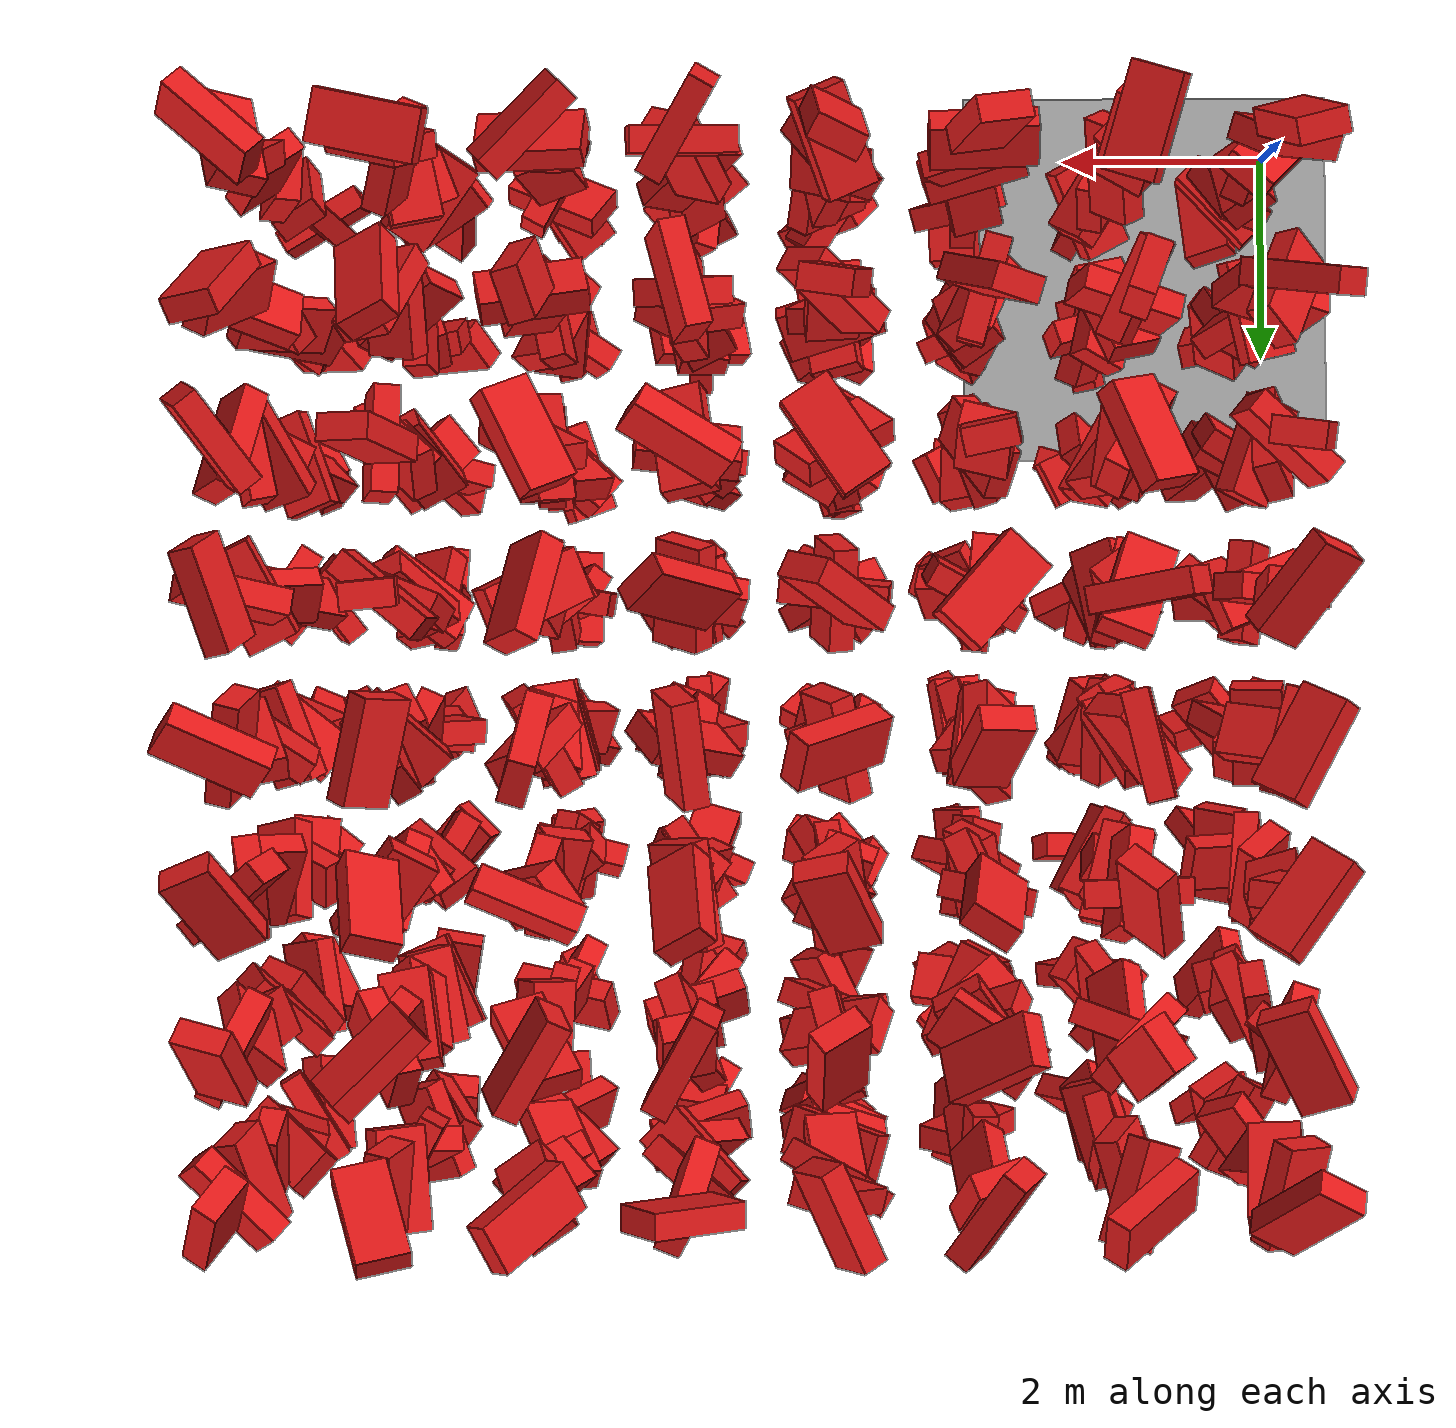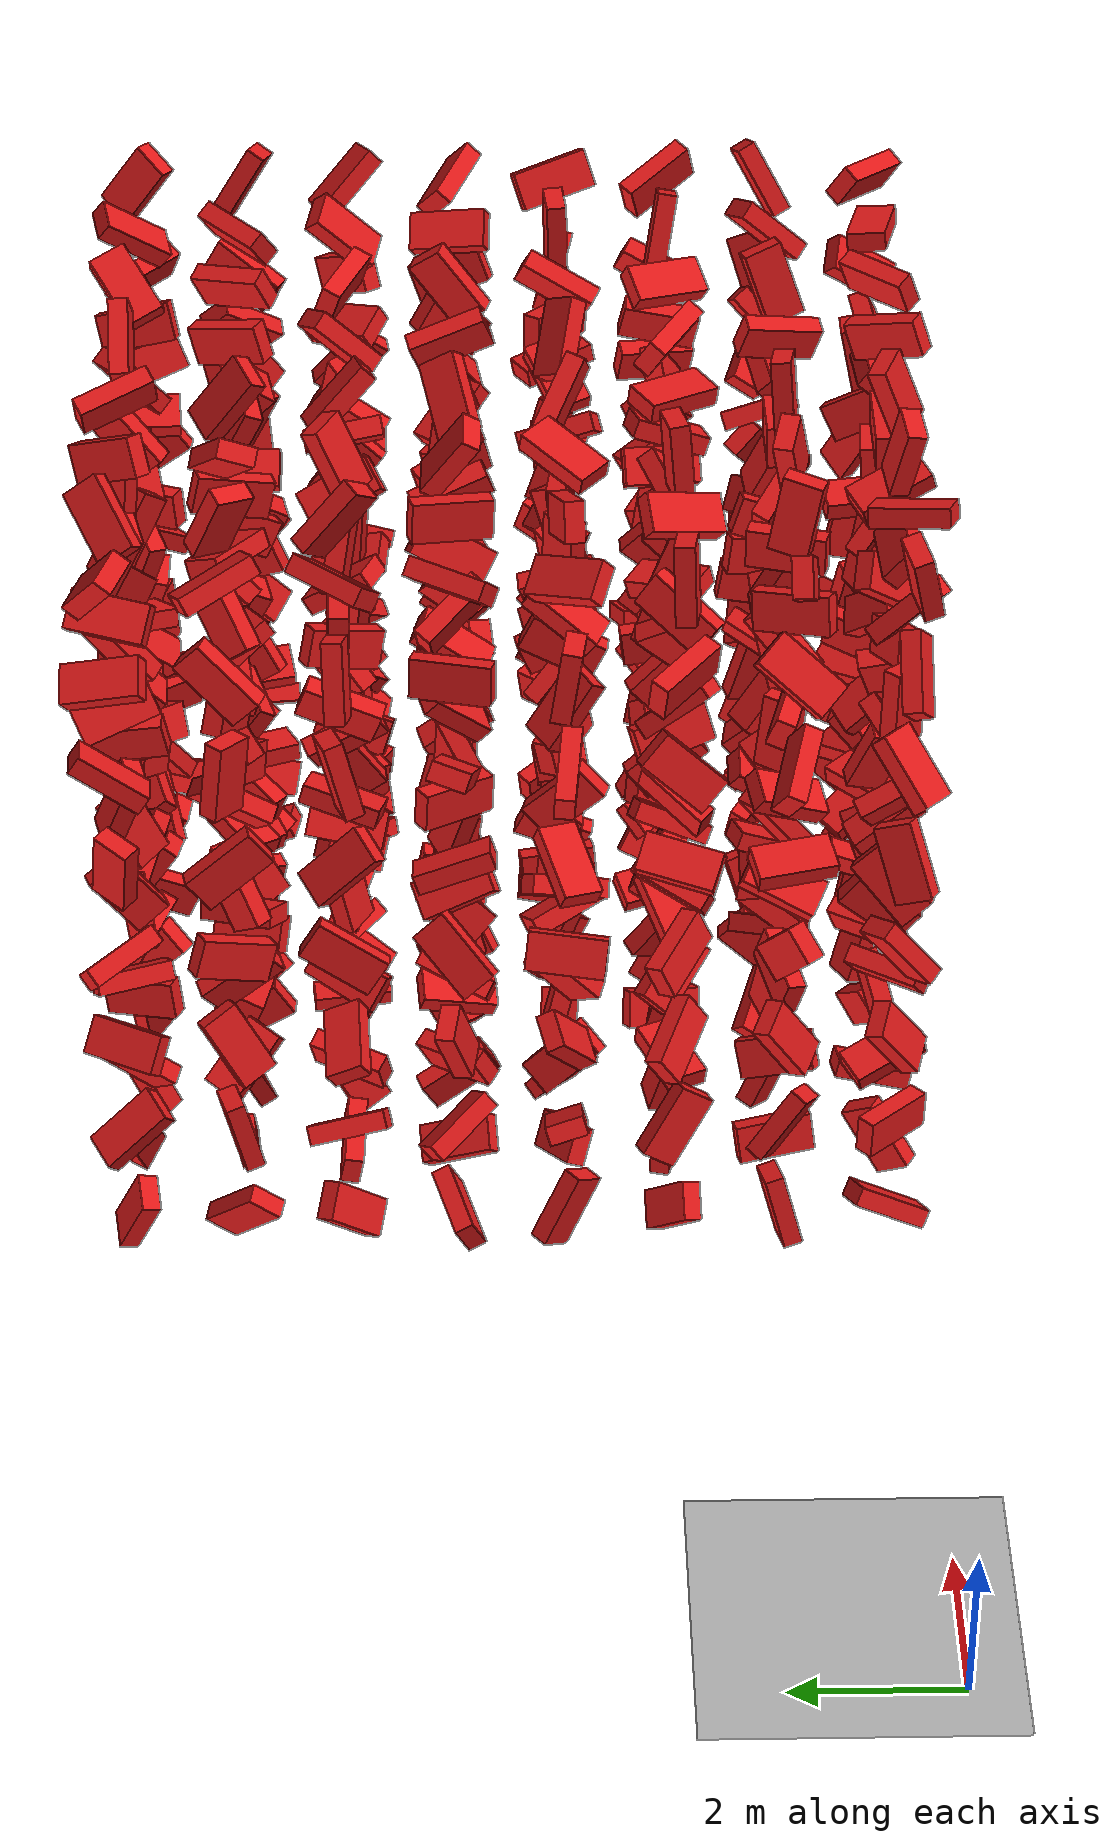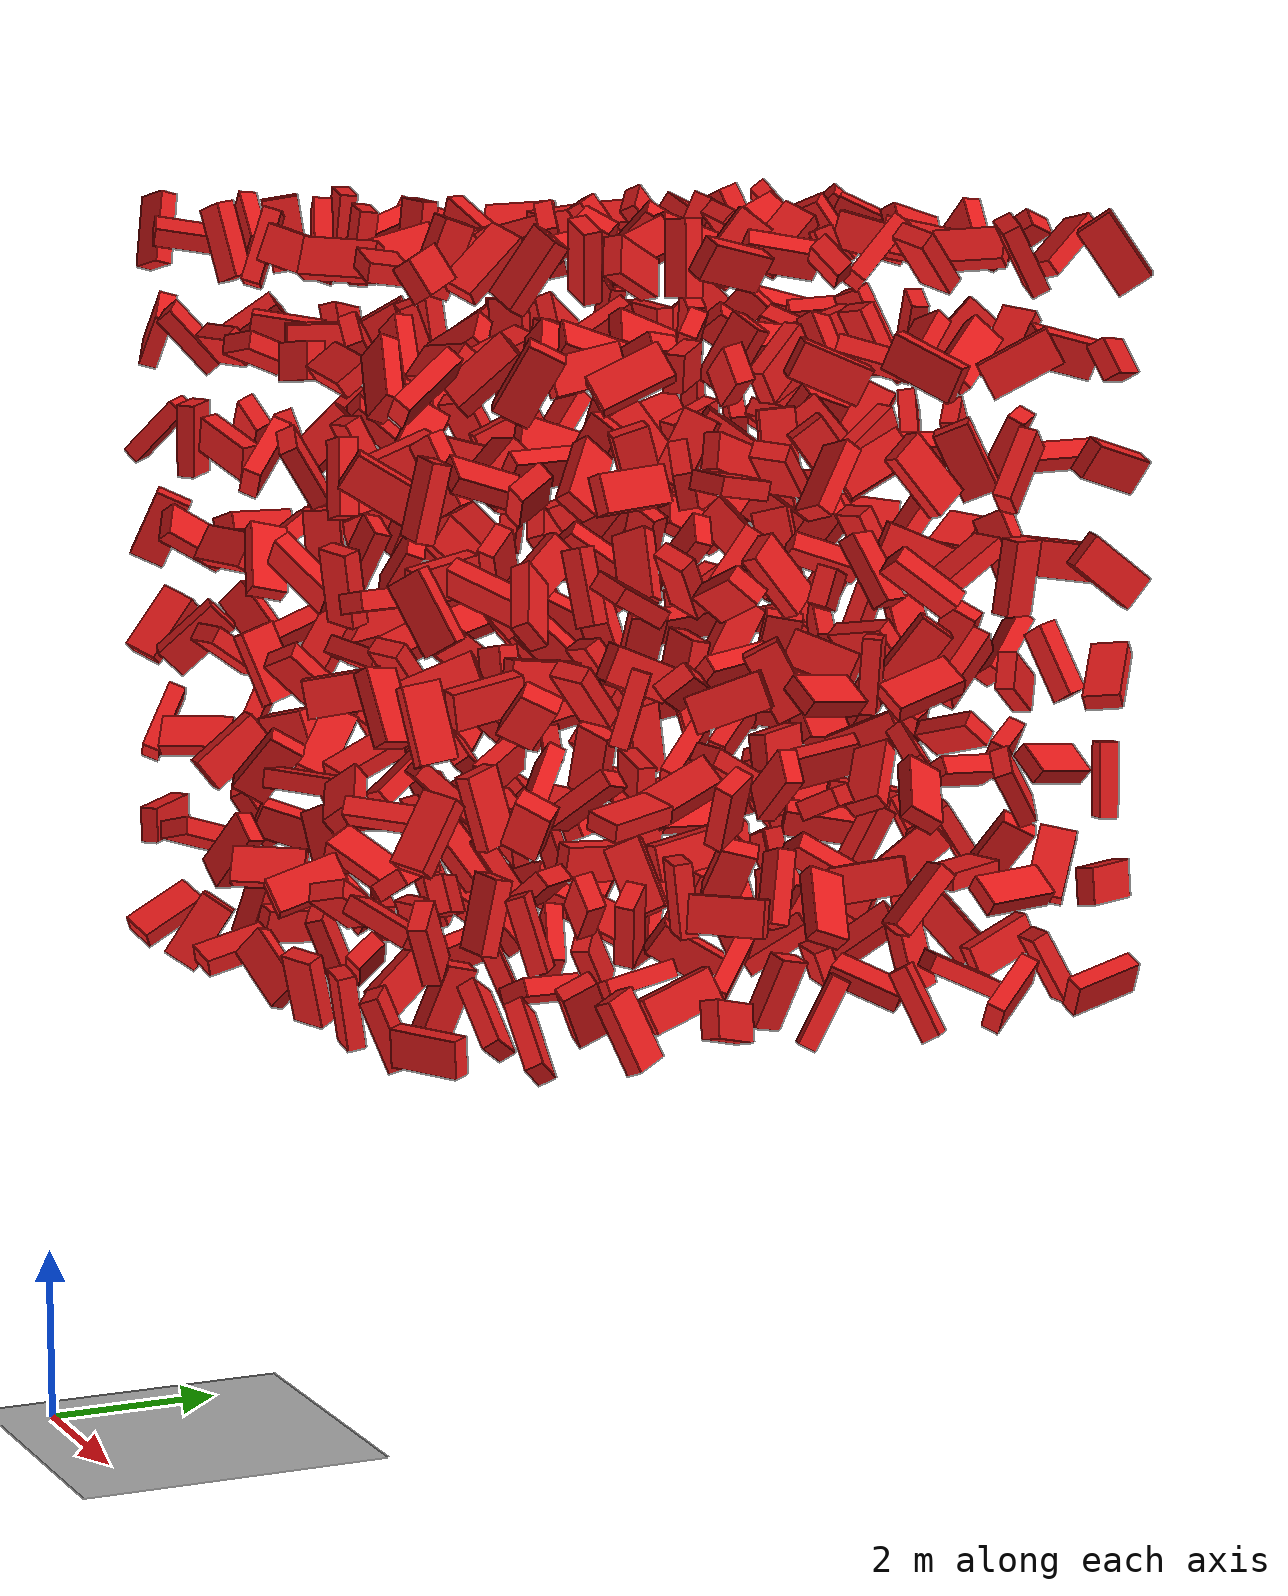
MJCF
<mujoco model="Humanoid and 100 objects">
    <compiler angle="degree"/>

    <option timestep="0.01" iterations="50" solver="PGS" jacobian="sparse" cone="elliptic" tolerance="1e-10"/>

    <size njmax="5000" nconmax="2000" nstack="1000000000"/>

    <default>
        <geom solimp=".9 .9 .01"/>

        <default class="object5">
			<geom type="box" material="geom" rgba=".9 .1 .1 1" size="0.400000 0.200000 0.100000"/>
        </default>
    </default>

    <asset>
        <texture type="skybox" builtin="gradient" width="128" height="128" rgb1=".4 .6 .8" rgb2="0 0 0"/>
        <texture name="texgeom" type="cube" builtin="flat" mark="cross" width="128" height="128"
            rgb1="0.6 0.6 0.6" rgb2="0.6 0.6 0.6" markrgb="1 1 1"/>
        <texture name="texplane" type="2d" builtin="checker" rgb1=".4 .4 .4" rgb2=".6 .6 .6"
            width="512" height="512"/>
        <material name='geom' texture="texgeom" texuniform="true"/>
        <material name='MatPlane' reflectance='0.3' texture="texplane" texrepeat="1 1" texuniform="true"/>
    </asset>

    <visual>
        <quality shadowsize="4096" offsamples="8"/>
        <map znear="0.1" force="0.05"/>
    </visual>

    <statistic extent="4"/>

    <worldbody>
        <light directional="true" diffuse=".8 .8 .8" pos="0 0 10" dir="0 0 -10"/>

        <geom pos="0 0 0" type="plane" size="3 3 .5" rgba=".7 .7 .7 1" material="MatPlane"/>
		<body pos="1.100234 1.100335 6.100607" quat="0.000306 0.732310 -0.602102 -0.318112"> <freejoint/> <geom class="object5"/> </body>
		<body pos="1.100461 1.100742 7.200664" quat="-0.644361 -0.654580 0.262578 0.295595"> <freejoint/> <geom class="object5"/> </body>
		<body pos="1.100667 1.100462 8.300946" quat="0.155772 -0.579217 -0.587160 -0.543586"> <freejoint/> <geom class="object5"/> </body>
		<body pos="1.100769 1.100589 9.400416" quat="0.479472 0.483493 -0.083918 0.727530"> <freejoint/> <geom class="object5"/> </body>
		<body pos="1.100564 1.100939 10.500304" quat="0.560505 0.013566 0.781842 -0.272715"> <freejoint/> <geom class="object5"/> </body>
		<body pos="1.100418 1.100858 11.600484" quat="0.847147 0.191666 -0.328033 0.371483"> <freejoint/> <geom class="object5"/> </body>
		<body pos="1.100162 1.100210 12.700163" quat="-0.315241 0.217604 -0.765923 -0.516365"> <freejoint/> <geom class="object5"/> </body>
		<body pos="1.100651 1.100236 13.800168" quat="-0.425508 -0.423093 0.439056 -0.668704"> <freejoint/> <geom class="object5"/> </body>
		<body pos="1.100456 2.200590 6.100842" quat="0.557197 0.330137 0.527595 -0.549713"> <freejoint/> <geom class="object5"/> </body>
		<body pos="1.100134 2.200263 7.200257" quat="-0.534900 0.531929 0.119762 0.645438"> <freejoint/> <geom class="object5"/> </body>
		<body pos="1.100498 2.200713 8.300062" quat="-0.564922 0.534442 -0.613366 -0.137901"> <freejoint/> <geom class="object5"/> </body>
		<body pos="1.100468 2.200285 9.400853" quat="-0.065366 -0.444028 0.498011 -0.741992"> <freejoint/> <geom class="object5"/> </body>
		<body pos="1.100853 2.200469 10.500730" quat="0.103970 -0.775114 0.614873 -0.101585"> <freejoint/> <geom class="object5"/> </body>
		<body pos="1.100715 2.200066 11.600942" quat="0.513693 0.816633 -0.229542 0.128611"> <freejoint/> <geom class="object5"/> </body>
		<body pos="1.100019 2.200485 12.700199" quat="-0.408972 -0.410055 0.113039 0.807353"> <freejoint/> <geom class="object5"/> </body>
		<body pos="1.100889 2.200023 13.800587" quat="-0.694104 -0.650805 -0.170777 0.255946"> <freejoint/> <geom class="object5"/> </body>
		<body pos="1.100518 3.300934 6.100957" quat="0.433164 -0.118737 -0.577026 -0.682138"> <freejoint/> <geom class="object5"/> </body>
		<body pos="1.100542 3.300611 7.200862" quat="-0.314584 0.759149 -0.104910 0.560111"> <freejoint/> <geom class="object5"/> </body>
		<body pos="1.100831 3.300486 8.300565" quat="-0.493819 0.820697 -0.062965 0.280419"> <freejoint/> <geom class="object5"/> </body>
		<body pos="1.100930 3.300348 9.400356" quat="0.549125 -0.780609 0.122025 -0.272434"> <freejoint/> <geom class="object5"/> </body>
		<body pos="1.100449 3.300467 10.500180" quat="-0.235581 0.530933 -0.777682 0.240461"> <freejoint/> <geom class="object5"/> </body>
		<body pos="1.100982 3.300269 11.600669" quat="-0.571154 0.391388 -0.703385 0.160775"> <freejoint/> <geom class="object5"/> </body>
		<body pos="1.100276 3.300408 12.700984" quat="0.597662 0.714250 -0.324215 -0.165926"> <freejoint/> <geom class="object5"/> </body>
		<body pos="1.100562 3.300121 13.800258" quat="0.469075 -0.425311 0.589902 0.501094"> <freejoint/> <geom class="object5"/> </body>
		<body pos="1.100701 4.400423 6.100622" quat="0.597434 -0.074392 0.657955 0.452365"> <freejoint/> <geom class="object5"/> </body>
		<body pos="1.100488 4.400916 7.200199" quat="-0.033463 0.258930 0.147002 0.954058"> <freejoint/> <geom class="object5"/> </body>
		<body pos="1.100742 4.400325 8.300044" quat="-0.236146 0.421415 0.757092 0.439836"> <freejoint/> <geom class="object5"/> </body>
		<body pos="1.100286 4.400363 9.400735" quat="-0.369693 0.546308 -0.649921 0.377462"> <freejoint/> <geom class="object5"/> </body>
		<body pos="1.100628 4.400476 10.500001" quat="-0.956153 -0.092899 0.206707 -0.185511"> <freejoint/> <geom class="object5"/> </body>
		<body pos="1.100702 4.400695 11.600617" quat="-0.131133 -0.200474 -0.702088 0.670586"> <freejoint/> <geom class="object5"/> </body>
		<body pos="1.100140 4.400220 12.700314" quat="0.496316 -0.492157 -0.432566 -0.569508"> <freejoint/> <geom class="object5"/> </body>
		<body pos="1.100807 4.400820 13.800348" quat="0.809849 -0.361351 -0.025731 0.461420"> <freejoint/> <geom class="object5"/> </body>
		<body pos="1.100161 5.500871 6.100765" quat="-0.011228 0.189106 -0.822910 -0.535661"> <freejoint/> <geom class="object5"/> </body>
		<body pos="1.100168 5.500048 7.200541" quat="0.810170 -0.376301 -0.038847 -0.447786"> <freejoint/> <geom class="object5"/> </body>
		<body pos="1.100320 5.500613 8.300736" quat="0.590512 -0.577044 0.488992 0.281430"> <freejoint/> <geom class="object5"/> </body>
		<body pos="1.100169 5.500942 9.400238" quat="0.804485 -0.294458 -0.467156 0.218779"> <freejoint/> <geom class="object5"/> </body>
		<body pos="1.100925 5.500637 10.500979" quat="0.684183 -0.039534 0.196111 0.701335"> <freejoint/> <geom class="object5"/> </body>
		<body pos="1.100385 5.500659 11.600610" quat="0.150129 -0.950132 0.097681 0.255282"> <freejoint/> <geom class="object5"/> </body>
		<body pos="1.100233 5.500999 12.700315" quat="-0.477724 -0.382418 0.508152 0.606068"> <freejoint/> <geom class="object5"/> </body>
		<body pos="1.100640 5.500911 13.800565" quat="0.148189 0.490870 -0.800053 -0.311450"> <freejoint/> <geom class="object5"/> </body>
		<body pos="1.100487 6.600114 6.100735" quat="0.063413 -0.529447 -0.630074 -0.564510"> <freejoint/> <geom class="object5"/> </body>
		<body pos="1.100069 6.600360 7.200443" quat="-0.310343 -0.643132 0.686594 0.136592"> <freejoint/> <geom class="object5"/> </body>
		<body pos="1.100995 6.600267 8.300230" quat="0.015760 -0.153093 0.241759 0.958053"> <freejoint/> <geom class="object5"/> </body>
		<body pos="1.100398 6.600800 9.400286" quat="-0.555853 0.365289 -0.679700 0.309192"> <freejoint/> <geom class="object5"/> </body>
		<body pos="1.100600 6.600034 10.500932" quat="0.695507 0.015616 -0.522079 -0.493416"> <freejoint/> <geom class="object5"/> </body>
		<body pos="1.100114 6.600453 11.600535" quat="0.509563 0.546814 -0.314319 0.585271"> <freejoint/> <geom class="object5"/> </body>
		<body pos="1.100506 6.600573 12.700134" quat="0.542038 -0.625018 -0.380123 -0.413586"> <freejoint/> <geom class="object5"/> </body>
		<body pos="1.100974 6.600615 13.800485" quat="0.104609 0.443147 -0.832544 -0.315512"> <freejoint/> <geom class="object5"/> </body>
		<body pos="1.100285 7.700886 6.100161" quat="-0.215128 0.486725 -0.263388 0.804640"> <freejoint/> <geom class="object5"/> </body>
		<body pos="1.100858 7.700698 7.200314" quat="0.486502 0.517488 -0.347944 0.611929"> <freejoint/> <geom class="object5"/> </body>
		<body pos="1.100020 7.700138 8.300165" quat="-0.755763 0.001367 0.567889 -0.326071"> <freejoint/> <geom class="object5"/> </body>
		<body pos="1.100273 7.700477 9.400097" quat="0.241430 0.506464 0.556482 0.612807"> <freejoint/> <geom class="object5"/> </body>
		<body pos="1.100864 7.700897 10.500490" quat="-0.579811 -0.270727 -0.679438 -0.359014"> <freejoint/> <geom class="object5"/> </body>
		<body pos="1.100523 7.700789 11.600603" quat="-0.627476 0.256279 -0.645907 -0.351283"> <freejoint/> <geom class="object5"/> </body>
		<body pos="1.100989 7.700808 12.700249" quat="-0.171320 -0.597078 0.389212 0.680192"> <freejoint/> <geom class="object5"/> </body>
		<body pos="1.100346 7.700296 13.800221" quat="0.801964 -0.273689 -0.017283 -0.530706"> <freejoint/> <geom class="object5"/> </body>
		<body pos="1.100697 8.800809 6.100556" quat="-0.537205 -0.600583 -0.529325 0.265566"> <freejoint/> <geom class="object5"/> </body>
		<body pos="1.100089 8.800314 7.200276" quat="-0.047456 -0.772866 0.500447 -0.387272"> <freejoint/> <geom class="object5"/> </body>
		<body pos="1.100935 8.800916 8.300575" quat="0.776889 -0.385810 -0.198427 0.456313"> <freejoint/> <geom class="object5"/> </body>
		<body pos="1.100973 8.800661 9.400092" quat="0.457712 0.061631 0.393504 0.794894"> <freejoint/> <geom class="object5"/> </body>
		<body pos="1.100180 8.800108 10.500547" quat="-0.585741 0.170581 0.738052 0.288251"> <freejoint/> <geom class="object5"/> </body>
		<body pos="1.100534 8.800220 11.600300" quat="-0.272697 0.674919 0.668855 0.150845"> <freejoint/> <geom class="object5"/> </body>
		<body pos="1.100009 8.800432 12.700650" quat="-0.696380 0.333143 0.114629 -0.625245"> <freejoint/> <geom class="object5"/> </body>
		<body pos="1.100564 8.800154 13.800455" quat="0.393718 -0.270724 -0.352692 -0.804551"> <freejoint/> <geom class="object5"/> </body>
		<body pos="2.200541 1.100218 6.100971" quat="-0.624511 0.021465 -0.685070 0.374438"> <freejoint/> <geom class="object5"/> </body>
		<body pos="2.200155 1.100916 7.200374" quat="-0.020699 0.832055 -0.518280 0.196575"> <freejoint/> <geom class="object5"/> </body>
		<body pos="2.200817 1.100113 8.300536" quat="0.800501 0.353590 0.191912 0.444232"> <freejoint/> <geom class="object5"/> </body>
		<body pos="2.200966 1.100055 9.400920" quat="-0.514363 0.226398 -0.776163 0.285910"> <freejoint/> <geom class="object5"/> </body>
		<body pos="2.200636 1.100269 10.500454" quat="0.478902 0.560115 -0.664980 -0.121347"> <freejoint/> <geom class="object5"/> </body>
		<body pos="2.200953 1.100455 11.600084" quat="0.238955 0.622862 0.289106 -0.686557"> <freejoint/> <geom class="object5"/> </body>
		<body pos="2.200357 1.100478 12.700562" quat="-0.487245 0.420320 0.106664 0.757988"> <freejoint/> <geom class="object5"/> </body>
		<body pos="2.200991 1.100939 13.800114" quat="-0.151895 -0.585054 0.793140 0.074618"> <freejoint/> <geom class="object5"/> </body>
		<body pos="2.200104 2.200253 6.100890" quat="-0.440086 0.636570 -0.488373 0.403230"> <freejoint/> <geom class="object5"/> </body>
		<body pos="2.200154 2.200073 7.200577" quat="-0.204363 0.573725 -0.605028 0.512852"> <freejoint/> <geom class="object5"/> </body>
		<body pos="2.200332 2.200986 8.300251" quat="-0.770765 0.612010 0.174075 -0.032612"> <freejoint/> <geom class="object5"/> </body>
		<body pos="2.200394 2.200960 9.400032" quat="-0.325997 0.535332 -0.774005 0.089790"> <freejoint/> <geom class="object5"/> </body>
		<body pos="2.200360 2.200713 10.500007" quat="0.287349 -0.769448 0.565212 0.076917"> <freejoint/> <geom class="object5"/> </body>
		<body pos="2.200593 2.200119 11.600612" quat="-0.017270 -0.196100 -0.789553 0.581251"> <freejoint/> <geom class="object5"/> </body>
		<body pos="2.200891 2.200754 12.700800" quat="-0.464762 -0.285864 0.554249 0.628558"> <freejoint/> <geom class="object5"/> </body>
		<body pos="2.200952 2.200500 13.800630" quat="-0.687276 -0.182304 -0.699985 0.066622"> <freejoint/> <geom class="object5"/> </body>
		<body pos="2.200422 3.300779 6.100769" quat="-0.701985 -0.697774 0.072691 0.122656"> <freejoint/> <geom class="object5"/> </body>
		<body pos="2.200312 3.300205 7.200619" quat="-0.070671 0.226734 -0.970890 -0.031157"> <freejoint/> <geom class="object5"/> </body>
		<body pos="2.200344 3.300123 8.300480" quat="-0.143122 0.401350 0.364925 -0.827807"> <freejoint/> <geom class="object5"/> </body>
		<body pos="2.200226 3.300134 9.400537" quat="-0.754870 -0.411891 -0.091480 -0.502143"> <freejoint/> <geom class="object5"/> </body>
		<body pos="2.200887 3.300573 10.500608" quat="0.080862 0.463218 -0.676534 -0.566739"> <freejoint/> <geom class="object5"/> </body>
		<body pos="2.200799 3.300782 11.600630" quat="-0.076016 -0.728130 -0.563302 0.383066"> <freejoint/> <geom class="object5"/> </body>
		<body pos="2.200441 3.300711 12.700958" quat="-0.457040 -0.727491 -0.205777 -0.468538"> <freejoint/> <geom class="object5"/> </body>
		<body pos="2.200233 3.300521 13.800381" quat="-0.552612 0.083449 0.347323 -0.753009"> <freejoint/> <geom class="object5"/> </body>
		<body pos="2.200463 4.400105 6.100354" quat="0.284917 -0.050346 -0.529990 -0.797119"> <freejoint/> <geom class="object5"/> </body>
		<body pos="2.200524 4.400384 7.200553" quat="0.672329 0.089135 -0.603222 -0.419704"> <freejoint/> <geom class="object5"/> </body>
		<body pos="2.200762 4.400055 8.300648" quat="-0.781201 0.036869 -0.513822 0.352637"> <freejoint/> <geom class="object5"/> </body>
		<body pos="2.200387 4.400411 9.400067" quat="-0.752352 0.175330 -0.291271 0.564257"> <freejoint/> <geom class="object5"/> </body>
		<body pos="2.200967 4.400094 10.500058" quat="0.667440 0.355396 0.628790 0.181219"> <freejoint/> <geom class="object5"/> </body>
		<body pos="2.200788 4.400360 11.600898" quat="-0.758606 0.153637 0.450111 0.445322"> <freejoint/> <geom class="object5"/> </body>
		<body pos="2.200711 4.400789 12.700491" quat="-0.252599 0.544111 -0.785210 -0.153568"> <freejoint/> <geom class="object5"/> </body>
		<body pos="2.200999 4.400581 13.800762" quat="-0.213853 0.086952 0.686540 0.689470"> <freejoint/> <geom class="object5"/> </body>
		<body pos="2.200453 5.500049 6.100749" quat="0.056620 -0.616204 0.677327 -0.397888"> <freejoint/> <geom class="object5"/> </body>
		<body pos="2.200810 5.500998 7.200872" quat="-0.314517 0.280290 -0.452466 0.785997"> <freejoint/> <geom class="object5"/> </body>
		<body pos="2.200440 5.500516 8.300105" quat="0.728380 0.388739 0.088626 0.557216"> <freejoint/> <geom class="object5"/> </body>
		<body pos="2.200989 5.500795 9.400644" quat="0.569131 -0.422306 -0.111797 0.696598"> <freejoint/> <geom class="object5"/> </body>
		<body pos="2.200658 5.500598 10.500311" quat="-0.629541 0.620648 -0.360438 0.297589"> <freejoint/> <geom class="object5"/> </body>
		<body pos="2.200801 5.500600 11.600149" quat="-0.515533 -0.230560 0.312670 -0.763744"> <freejoint/> <geom class="object5"/> </body>
		<body pos="2.200153 5.500953 12.700992" quat="-0.554989 -0.683698 0.472491 0.036012"> <freejoint/> <geom class="object5"/> </body>
		<body pos="2.200568 5.500907 13.800661" quat="0.484534 -0.387526 -0.537907 0.570707"> <freejoint/> <geom class="object5"/> </body>
		<body pos="2.200049 6.600131 6.100298" quat="0.100381 -0.084157 0.643575 0.754090"> <freejoint/> <geom class="object5"/> </body>
		<body pos="2.200601 6.600811 7.200815" quat="-0.706612 -0.473773 -0.242963 -0.466055"> <freejoint/> <geom class="object5"/> </body>
		<body pos="2.200214 6.600329 8.300275" quat="0.374239 0.333767 -0.343024 -0.794279"> <freejoint/> <geom class="object5"/> </body>
		<body pos="2.200308 6.600340 9.400444" quat="-0.670397 -0.290854 0.550875 -0.403124"> <freejoint/> <geom class="object5"/> </body>
		<body pos="2.200978 6.600960 10.500848" quat="0.176067 -0.774279 -0.607752 -0.011410"> <freejoint/> <geom class="object5"/> </body>
		<body pos="2.200089 6.600930 11.600868" quat="0.544768 -0.517507 -0.592476 0.290493"> <freejoint/> <geom class="object5"/> </body>
		<body pos="2.200263 6.600308 12.700290" quat="0.689421 0.723701 0.029563 -0.009055"> <freejoint/> <geom class="object5"/> </body>
		<body pos="2.200881 6.600616 13.800145" quat="-0.554944 -0.503103 0.662381 -0.013258"> <freejoint/> <geom class="object5"/> </body>
		<body pos="2.200630 7.700395 6.100791" quat="0.293213 0.325376 -0.594246 0.674558"> <freejoint/> <geom class="object5"/> </body>
		<body pos="2.200323 7.700977 7.200515" quat="0.027728 -0.866922 0.322952 -0.378654"> <freejoint/> <geom class="object5"/> </body>
		<body pos="2.200984 7.700977 8.300947" quat="-0.636705 -0.183226 -0.587524 -0.464597"> <freejoint/> <geom class="object5"/> </body>
		<body pos="2.200931 7.700335 9.400332" quat="-0.055219 0.556752 -0.424721 -0.711751"> <freejoint/> <geom class="object5"/> </body>
		<body pos="2.200854 7.700882 10.500869" quat="-0.519402 -0.443465 -0.100542 -0.723500"> <freejoint/> <geom class="object5"/> </body>
		<body pos="2.200627 7.700092 11.600576" quat="0.266395 0.032466 -0.725659 0.633561"> <freejoint/> <geom class="object5"/> </body>
		<body pos="2.200330 7.700952 12.700910" quat="0.761098 -0.432171 -0.483668 0.004778"> <freejoint/> <geom class="object5"/> </body>
		<body pos="2.200534 7.700046 13.800041" quat="0.786703 -0.095081 0.537419 0.288511"> <freejoint/> <geom class="object5"/> </body>
		<body pos="2.200529 8.800956 6.100404" quat="0.473039 0.768266 0.194033 -0.385166"> <freejoint/> <geom class="object5"/> </body>
		<body pos="2.200873 8.800056 7.200199" quat="0.754859 -0.085017 0.497771 -0.418549"> <freejoint/> <geom class="object5"/> </body>
		<body pos="2.200989 8.800600 8.300420" quat="0.771760 -0.237433 0.152227 -0.569946"> <freejoint/> <geom class="object5"/> </body>
		<body pos="2.200599 8.800558 9.400582" quat="-0.330837 -0.672152 0.104350 0.654118"> <freejoint/> <geom class="object5"/> </body>
		<body pos="2.200369 8.800479 10.500890" quat="0.467311 0.527276 0.637099 -0.312578"> <freejoint/> <geom class="object5"/> </body>
		<body pos="2.200048 8.800159 11.600123" quat="0.291306 -0.742760 0.463305 -0.385742"> <freejoint/> <geom class="object5"/> </body>
		<body pos="2.200910 8.800268 12.700952" quat="-0.269953 0.534869 -0.739980 0.305728"> <freejoint/> <geom class="object5"/> </body>
		<body pos="2.200270 8.800806 13.800886" quat="-0.860083 0.300782 0.392969 -0.123945"> <freejoint/> <geom class="object5"/> </body>
		<body pos="3.300183 1.100764 6.100160" quat="-0.186278 0.680159 0.708843 -0.015020"> <freejoint/> <geom class="object5"/> </body>
		<body pos="3.300350 1.100341 7.200780" quat="0.640376 0.631420 -0.189863 0.393927"> <freejoint/> <geom class="object5"/> </body>
		<body pos="3.300445 1.100694 8.300746" quat="-0.629210 0.300985 -0.645014 0.312187"> <freejoint/> <geom class="object5"/> </body>
		<body pos="3.300665 1.100022 9.400304" quat="-0.757479 0.177136 0.228492 0.585354"> <freejoint/> <geom class="object5"/> </body>
		<body pos="3.300712 1.100942 10.500482" quat="0.115303 -0.078892 0.486534 -0.862419"> <freejoint/> <geom class="object5"/> </body>
		<body pos="3.300290 1.100566 11.600401" quat="-0.725604 0.651483 -0.041888 -0.217519"> <freejoint/> <geom class="object5"/> </body>
		<body pos="3.300218 1.100575 12.700471" quat="0.013355 0.017610 -0.414180 -0.909927"> <freejoint/> <geom class="object5"/> </body>
		<body pos="3.300314 1.100066 13.800139" quat="-0.354107 -0.509589 0.553540 -0.555447"> <freejoint/> <geom class="object5"/> </body>
		<body pos="3.300932 2.200841 6.100462" quat="-0.597929 -0.481053 0.622200 -0.154713"> <freejoint/> <geom class="object5"/> </body>
		<body pos="3.300294 2.200883 7.200869" quat="0.470673 -0.677035 0.272007 0.496088"> <freejoint/> <geom class="object5"/> </body>
		<body pos="3.300262 2.200071 8.300601" quat="-0.816399 0.064821 -0.485018 0.306673"> <freejoint/> <geom class="object5"/> </body>
		<body pos="3.300019 2.200846 9.400216" quat="0.460109 -0.460142 -0.749429 -0.122171"> <freejoint/> <geom class="object5"/> </body>
		<body pos="3.300591 2.200971 10.500683" quat="-0.159735 -0.710769 0.220338 -0.648648"> <freejoint/> <geom class="object5"/> </body>
		<body pos="3.300318 2.200607 11.600401" quat="0.553326 0.589188 -0.018945 0.588497"> <freejoint/> <geom class="object5"/> </body>
		<body pos="3.300073 2.200194 12.700002" quat="0.434188 0.418219 -0.556520 -0.571716"> <freejoint/> <geom class="object5"/> </body>
		<body pos="3.300326 2.200803 13.800532" quat="0.647299 -0.552494 0.452720 0.266081"> <freejoint/> <geom class="object5"/> </body>
		<body pos="3.300813 3.300781 6.100440" quat="0.372691 0.600511 -0.527100 0.471862"> <freejoint/> <geom class="object5"/> </body>
		<body pos="3.300311 3.300272 7.200826" quat="-0.498082 -0.545839 0.564401 -0.368002"> <freejoint/> <geom class="object5"/> </body>
		<body pos="3.300376 3.300020 8.300595" quat="0.048471 -0.927729 -0.220282 -0.297398"> <freejoint/> <geom class="object5"/> </body>
		<body pos="3.300117 3.300522 9.400886" quat="0.650578 0.318756 0.041362 0.688064"> <freejoint/> <geom class="object5"/> </body>
		<body pos="3.300346 3.300365 10.500011" quat="-0.709439 -0.420159 0.377296 0.421676"> <freejoint/> <geom class="object5"/> </body>
		<body pos="3.300342 3.300057 11.600196" quat="0.161939 0.820160 -0.250866 -0.488037"> <freejoint/> <geom class="object5"/> </body>
		<body pos="3.300134 3.300884 12.700482" quat="-0.471170 -0.523364 0.631160 -0.325155"> <freejoint/> <geom class="object5"/> </body>
		<body pos="3.300331 3.300508 13.800033" quat="0.552853 0.407539 0.544679 -0.481239"> <freejoint/> <geom class="object5"/> </body>
		<body pos="3.300307 4.400818 6.100137" quat="0.388469 0.864877 -0.204588 -0.243360"> <freejoint/> <geom class="object5"/> </body>
		<body pos="3.300056 4.400128 7.200102" quat="0.328917 0.469591 0.637121 -0.515145"> <freejoint/> <geom class="object5"/> </body>
		<body pos="3.300173 4.400485 8.300937" quat="0.017397 -0.514346 -0.813166 0.271859"> <freejoint/> <geom class="object5"/> </body>
		<body pos="3.300403 4.400221 9.400048" quat="-0.063387 0.133095 0.433660 0.888936"> <freejoint/> <geom class="object5"/> </body>
		<body pos="3.300503 4.400374 10.500755" quat="-0.134884 0.220681 0.620597 -0.740247"> <freejoint/> <geom class="object5"/> </body>
		<body pos="3.300505 4.400815 11.600380" quat="-0.567138 0.352836 -0.624262 0.405166"> <freejoint/> <geom class="object5"/> </body>
		<body pos="3.300703 4.400878 12.700846" quat="-0.272825 -0.631947 0.305816 -0.657788"> <freejoint/> <geom class="object5"/> </body>
		<body pos="3.300510 4.400437 13.800282" quat="0.399629 0.141144 0.006065 -0.905725"> <freejoint/> <geom class="object5"/> </body>
		<body pos="3.300913 5.500278 6.100691" quat="-0.573984 -0.223902 -0.610737 -0.497404"> <freejoint/> <geom class="object5"/> </body>
		<body pos="3.300215 5.500926 7.200687" quat="-0.199552 0.734301 -0.648562 0.018641"> <freejoint/> <geom class="object5"/> </body>
		<body pos="3.300805 5.500730 8.300597" quat="-0.643084 0.077355 0.644441 -0.406393"> <freejoint/> <geom class="object5"/> </body>
		<body pos="3.300396 5.500255 9.400422" quat="0.248615 0.617313 -0.468610 0.580965"> <freejoint/> <geom class="object5"/> </body>
		<body pos="3.300686 5.500721 10.500391" quat="0.510982 0.194052 0.522581 -0.654331"> <freejoint/> <geom class="object5"/> </body>
		<body pos="3.300026 5.500011 11.600806" quat="-0.607962 -0.249113 -0.134262 0.741821"> <freejoint/> <geom class="object5"/> </body>
		<body pos="3.300982 5.500219 12.700370" quat="-0.482070 -0.502390 0.184693 0.693615"> <freejoint/> <geom class="object5"/> </body>
		<body pos="3.300159 5.500847 13.800741" quat="-0.270687 -0.560651 0.665339 -0.411976"> <freejoint/> <geom class="object5"/> </body>
		<body pos="3.300379 6.600952 6.100440" quat="-0.007880 -0.725974 -0.313945 -0.611832"> <freejoint/> <geom class="object5"/> </body>
		<body pos="3.300020 6.600135 7.200300" quat="-0.652303 0.357764 -0.296698 0.598729"> <freejoint/> <geom class="object5"/> </body>
		<body pos="3.300174 6.600809 8.300017" quat="0.150490 -0.317480 -0.539531 -0.765157"> <freejoint/> <geom class="object5"/> </body>
		<body pos="3.300824 6.600718 9.400770" quat="0.701391 -0.281267 -0.331422 0.564888"> <freejoint/> <geom class="object5"/> </body>
		<body pos="3.300414 6.600478 10.500729" quat="-0.629851 -0.148871 -0.479005 -0.593025"> <freejoint/> <geom class="object5"/> </body>
		<body pos="3.300934 6.600575 11.600309" quat="-0.488998 0.257068 0.596770 -0.581947"> <freejoint/> <geom class="object5"/> </body>
		<body pos="3.300711 6.600868 12.700742" quat="0.621728 0.587084 -0.435970 0.280563"> <freejoint/> <geom class="object5"/> </body>
		<body pos="3.300588 6.600370 13.800505" quat="0.514511 -0.433186 0.707442 0.217150"> <freejoint/> <geom class="object5"/> </body>
		<body pos="3.300576 7.700444 6.100600" quat="-0.394635 0.760929 -0.340094 -0.386763"> <freejoint/> <geom class="object5"/> </body>
		<body pos="3.300759 7.700259 7.200131" quat="0.206041 -0.968759 0.082211 0.110877"> <freejoint/> <geom class="object5"/> </body>
		<body pos="3.300266 7.700586 8.300235" quat="-0.525689 0.158473 -0.119191 0.827243"> <freejoint/> <geom class="object5"/> </body>
		<body pos="3.300037 7.700196 9.400021" quat="0.130166 -0.927218 -0.340409 -0.086285"> <freejoint/> <geom class="object5"/> </body>
		<body pos="3.300875 7.700690 10.500232" quat="-0.019405 0.269075 -0.503200 0.820982"> <freejoint/> <geom class="object5"/> </body>
		<body pos="3.300921 7.700116 11.600939" quat="-0.154853 -0.470057 -0.846380 0.196741"> <freejoint/> <geom class="object5"/> </body>
		<body pos="3.300917 7.700646 12.700627" quat="-0.936922 0.175201 -0.100783 0.285175"> <freejoint/> <geom class="object5"/> </body>
		<body pos="3.300527 7.700745 13.800618" quat="0.150280 -0.351111 0.160344 -0.910179"> <freejoint/> <geom class="object5"/> </body>
		<body pos="3.300149 8.800547 6.100865" quat="-0.675713 -0.129690 -0.599580 0.408774"> <freejoint/> <geom class="object5"/> </body>
		<body pos="3.300253 8.800084 7.200093" quat="0.588833 0.582519 0.463521 0.314795"> <freejoint/> <geom class="object5"/> </body>
		<body pos="3.300119 8.800908 8.300438" quat="0.558865 -0.701477 -0.348730 -0.272004"> <freejoint/> <geom class="object5"/> </body>
		<body pos="3.300258 8.800765 9.400516" quat="-0.682675 -0.095724 0.617891 -0.378157"> <freejoint/> <geom class="object5"/> </body>
		<body pos="3.300682 8.800415 10.500007" quat="0.587560 0.435729 0.487058 0.477167"> <freejoint/> <geom class="object5"/> </body>
		<body pos="3.300521 8.800655 11.600121" quat="0.400321 0.537191 -0.020376 0.742128"> <freejoint/> <geom class="object5"/> </body>
		<body pos="3.300155 8.800759 12.700193" quat="0.246770 0.600160 -0.552611 0.523005"> <freejoint/> <geom class="object5"/> </body>
		<body pos="3.300087 8.800507 13.800354" quat="-0.610947 0.616593 0.140003 -0.476399"> <freejoint/> <geom class="object5"/> </body>
		<body pos="4.400091 1.100524 6.100343" quat="0.491008 -0.795686 0.071623 0.347368"> <freejoint/> <geom class="object5"/> </body>
		<body pos="4.400760 1.100425 7.200248" quat="-0.757490 -0.444974 -0.249263 -0.407523"> <freejoint/> <geom class="object5"/> </body>
		<body pos="4.400255 1.100588 8.300650" quat="-0.056762 -0.435958 0.269324 0.856845"> <freejoint/> <geom class="object5"/> </body>
		<body pos="4.400874 1.100831 9.400786" quat="0.048688 -0.778307 -0.167328 0.603216"> <freejoint/> <geom class="object5"/> </body>
		<body pos="4.400018 1.100112 10.500191" quat="0.453823 -0.072236 -0.884005 0.085804"> <freejoint/> <geom class="object5"/> </body>
		<body pos="4.400681 1.100744 11.600818" quat="0.656076 0.558579 0.039278 -0.505975"> <freejoint/> <geom class="object5"/> </body>
		<body pos="4.400546 1.100894 12.700550" quat="-0.546458 0.198295 -0.020607 -0.813411"> <freejoint/> <geom class="object5"/> </body>
		<body pos="4.400997 1.100992 13.800831" quat="0.483339 0.547073 0.244471 -0.638223"> <freejoint/> <geom class="object5"/> </body>
		<body pos="4.400911 2.200270 6.100992" quat="-0.083387 0.274134 0.324439 -0.901463"> <freejoint/> <geom class="object5"/> </body>
		<body pos="4.400043 2.200277 7.200074" quat="0.244820 -0.282623 0.118616 -0.919847"> <freejoint/> <geom class="object5"/> </body>
		<body pos="4.400075 2.200751 8.300050" quat="0.035375 -0.757193 0.612887 0.223107"> <freejoint/> <geom class="object5"/> </body>
		<body pos="4.400896 2.200821 9.400669" quat="0.238310 0.958683 0.154077 -0.019874"> <freejoint/> <geom class="object5"/> </body>
		<body pos="4.400662 2.200809 10.500147" quat="-0.534359 0.653548 0.442614 0.302372"> <freejoint/> <geom class="object5"/> </body>
		<body pos="4.400181 2.200071 11.600085" quat="0.599889 -0.395097 0.336517 0.608923"> <freejoint/> <geom class="object5"/> </body>
		<body pos="4.400617 2.200562 12.700835" quat="-0.062461 -0.447879 -0.684642 0.571636"> <freejoint/> <geom class="object5"/> </body>
		<body pos="4.400660 2.200373 13.800619" quat="-0.439239 -0.468283 -0.479366 0.598322"> <freejoint/> <geom class="object5"/> </body>
		<body pos="4.400611 3.300320 6.100286" quat="-0.526488 0.269918 0.482001 -0.646242"> <freejoint/> <geom class="object5"/> </body>
		<body pos="4.400676 3.300171 7.200569" quat="0.424670 -0.561462 -0.001245 -0.710222"> <freejoint/> <geom class="object5"/> </body>
		<body pos="4.400124 3.300659 8.300485" quat="-0.006658 -0.328962 -0.819895 0.468521"> <freejoint/> <geom class="object5"/> </body>
		<body pos="4.400013 3.300170 9.400166" quat="0.698123 0.341435 -0.556903 -0.293096"> <freejoint/> <geom class="object5"/> </body>
		<body pos="4.400691 3.300452 10.500025" quat="-0.386262 0.681755 -0.207118 0.585759"> <freejoint/> <geom class="object5"/> </body>
		<body pos="4.400427 3.300685 11.600905" quat="0.484261 -0.067010 -0.106523 -0.865825"> <freejoint/> <geom class="object5"/> </body>
		<body pos="4.400858 3.300431 12.700712" quat="-0.418957 0.842501 0.314465 0.125613"> <freejoint/> <geom class="object5"/> </body>
		<body pos="4.400617 3.300138 13.800682" quat="-0.062789 0.881528 -0.467661 -0.016112"> <freejoint/> <geom class="object5"/> </body>
		<body pos="4.400724 4.400988 6.100832" quat="0.672971 0.640296 0.148553 -0.339209"> <freejoint/> <geom class="object5"/> </body>
		<body pos="4.400959 4.400955 7.200662" quat="-0.123724 -0.551307 -0.537037 0.626374"> <freejoint/> <geom class="object5"/> </body>
		<body pos="4.400927 4.400850 8.300015" quat="-0.051599 0.217928 0.727440 -0.648595"> <freejoint/> <geom class="object5"/> </body>
		<body pos="4.400643 4.400422 9.400632" quat="-0.643041 0.655902 -0.049610 -0.392211"> <freejoint/> <geom class="object5"/> </body>
		<body pos="4.400132 4.400632 10.500458" quat="-0.557446 0.014454 -0.595273 -0.578528"> <freejoint/> <geom class="object5"/> </body>
		<body pos="4.400594 4.400711 11.600233" quat="0.497123 -0.475363 0.310182 -0.656266"> <freejoint/> <geom class="object5"/> </body>
		<body pos="4.400527 4.400210 12.700507" quat="0.008262 0.067909 0.747210 0.661058"> <freejoint/> <geom class="object5"/> </body>
		<body pos="4.400604 4.400932 13.800655" quat="-0.617099 -0.641631 0.441009 -0.114061"> <freejoint/> <geom class="object5"/> </body>
		<body pos="4.400236 5.500753 6.100564" quat="0.390997 -0.865405 0.294871 0.106052"> <freejoint/> <geom class="object5"/> </body>
		<body pos="4.400934 5.500000 7.200084" quat="0.695583 -0.192508 -0.691803 -0.022668"> <freejoint/> <geom class="object5"/> </body>
		<body pos="4.400243 5.500305 8.300081" quat="0.730398 0.122985 -0.671852 -0.002940"> <freejoint/> <geom class="object5"/> </body>
		<body pos="4.400486 5.500428 9.400397" quat="-0.092376 0.449672 -0.093295 -0.883492"> <freejoint/> <geom class="object5"/> </body>
		<body pos="4.400250 5.500488 10.500624" quat="-0.404001 -0.311826 -0.706091 0.490901"> <freejoint/> <geom class="object5"/> </body>
		<body pos="4.400471 5.500604 11.600552" quat="0.450001 0.045839 -0.842172 -0.293503"> <freejoint/> <geom class="object5"/> </body>
		<body pos="4.400204 5.500031 12.700225" quat="-0.477056 -0.601303 0.611797 0.191198"> <freejoint/> <geom class="object5"/> </body>
		<body pos="4.400707 5.500531 13.800378" quat="-0.016114 -0.351072 0.293695 0.888950"> <freejoint/> <geom class="object5"/> </body>
		<body pos="4.400640 6.600623 6.100732" quat="0.172993 0.798925 0.302231 -0.490357"> <freejoint/> <geom class="object5"/> </body>
		<body pos="4.400114 6.600921 7.200031" quat="-0.891153 0.389613 -0.185493 0.140141"> <freejoint/> <geom class="object5"/> </body>
		<body pos="4.400458 6.600727 8.300671" quat="0.614184 0.584910 -0.053102 -0.527104"> <freejoint/> <geom class="object5"/> </body>
		<body pos="4.400882 6.600207 9.400963" quat="0.643053 -0.164737 -0.710650 0.233068"> <freejoint/> <geom class="object5"/> </body>
		<body pos="4.400792 6.600956 10.500556" quat="0.452773 -0.810572 0.002840 0.371433"> <freejoint/> <geom class="object5"/> </body>
		<body pos="4.400347 6.600583 11.600154" quat="-0.786699 0.163501 -0.256976 -0.536969"> <freejoint/> <geom class="object5"/> </body>
		<body pos="4.400070 6.600477 12.700725" quat="-0.416320 -0.516239 -0.740969 -0.105546"> <freejoint/> <geom class="object5"/> </body>
		<body pos="4.400230 6.600440 13.800745" quat="-0.544286 0.214546 -0.319899 -0.745243"> <freejoint/> <geom class="object5"/> </body>
		<body pos="4.400817 7.700071 6.100625" quat="0.356703 -0.626669 -0.320857 0.614084"> <freejoint/> <geom class="object5"/> </body>
		<body pos="4.400673 7.700303 7.200572" quat="-0.407590 -0.733476 -0.512972 -0.180948"> <freejoint/> <geom class="object5"/> </body>
		<body pos="4.400922 7.700206 8.300059" quat="-0.195602 0.496820 0.721402 -0.441009"> <freejoint/> <geom class="object5"/> </body>
		<body pos="4.400720 7.700986 9.400973" quat="-0.667871 -0.689926 -0.047157 0.275185"> <freejoint/> <geom class="object5"/> </body>
		<body pos="4.400116 7.700027 10.500182" quat="0.665961 -0.637679 -0.331258 -0.200325"> <freejoint/> <geom class="object5"/> </body>
		<body pos="4.400668 7.700429 11.600593" quat="-0.878709 -0.363188 -0.308357 0.029670"> <freejoint/> <geom class="object5"/> </body>
		<body pos="4.400820 7.700086 12.700205" quat="0.346962 0.504656 0.518614 0.596641"> <freejoint/> <geom class="object5"/> </body>
		<body pos="4.400802 7.700880 13.800146" quat="0.690055 -0.111622 -0.498922 -0.512291"> <freejoint/> <geom class="object5"/> </body>
		<body pos="4.400552 8.800188 6.100298" quat="0.380299 0.761330 0.217288 -0.478053"> <freejoint/> <geom class="object5"/> </body>
		<body pos="4.400132 8.800037 7.200351" quat="-0.532101 -0.800133 0.276423 -0.015651"> <freejoint/> <geom class="object5"/> </body>
		<body pos="4.400834 8.800061 8.300338" quat="-0.409361 -0.844070 0.278386 -0.206084"> <freejoint/> <geom class="object5"/> </body>
		<body pos="4.400753 8.800692 9.400717" quat="-0.136869 -0.252429 0.012666 -0.957803"> <freejoint/> <geom class="object5"/> </body>
		<body pos="4.400911 8.800647 10.500848" quat="0.251404 -0.610129 -0.675693 -0.328601"> <freejoint/> <geom class="object5"/> </body>
		<body pos="4.400335 8.800727 11.600751" quat="-0.078563 0.392574 0.521198 0.753702"> <freejoint/> <geom class="object5"/> </body>
		<body pos="4.400628 8.800048 12.700108" quat="0.438470 -0.309493 0.652499 0.534980"> <freejoint/> <geom class="object5"/> </body>
		<body pos="4.400198 8.800879 13.800247" quat="0.487883 0.674607 -0.519007 -0.193669"> <freejoint/> <geom class="object5"/> </body>
		<body pos="5.500649 1.100475 6.100108" quat="0.408378 -0.464630 0.337782 0.709401"> <freejoint/> <geom class="object5"/> </body>
		<body pos="5.500611 1.100065 7.200567" quat="0.633499 -0.222282 0.449128 -0.589537"> <freejoint/> <geom class="object5"/> </body>
		<body pos="5.500563 1.100949 8.300500" quat="-0.340066 0.009872 0.068561 0.937847"> <freejoint/> <geom class="object5"/> </body>
		<body pos="5.500243 1.100652 9.400584" quat="-0.421512 -0.519671 -0.741722 0.046029"> <freejoint/> <geom class="object5"/> </body>
		<body pos="5.500658 1.100330 10.500168" quat="-0.530669 -0.720373 -0.429660 0.121846"> <freejoint/> <geom class="object5"/> </body>
		<body pos="5.500406 1.100163 11.600369" quat="0.126692 0.573716 0.608835 -0.533028"> <freejoint/> <geom class="object5"/> </body>
		<body pos="5.500232 1.100276 12.700810" quat="0.688448 -0.723280 -0.039955 -0.036191"> <freejoint/> <geom class="object5"/> </body>
		<body pos="5.500129 1.100366 13.800485" quat="0.434063 0.260858 -0.684721 -0.524118"> <freejoint/> <geom class="object5"/> </body>
		<body pos="5.500637 2.200415 6.100074" quat="0.649494 -0.260545 0.648891 -0.298687"> <freejoint/> <geom class="object5"/> </body>
		<body pos="5.500695 2.200645 7.200562" quat="0.958299 0.199983 -0.198264 0.048594"> <freejoint/> <geom class="object5"/> </body>
		<body pos="5.500878 2.200461 8.300435" quat="0.140319 -0.635486 -0.694044 -0.307849"> <freejoint/> <geom class="object5"/> </body>
		<body pos="5.500757 2.200768 9.400090" quat="-0.313585 -0.475761 -0.786675 0.237609"> <freejoint/> <geom class="object5"/> </body>
		<body pos="5.500706 2.200780 10.500847" quat="0.273276 0.289841 0.490915 -0.774800"> <freejoint/> <geom class="object5"/> </body>
		<body pos="5.500880 2.200447 11.600821" quat="0.481204 0.545219 -0.329601 -0.602115"> <freejoint/> <geom class="object5"/> </body>
		<body pos="5.500004 2.200934 12.700732" quat="0.575286 -0.642517 0.360885 0.354938"> <freejoint/> <geom class="object5"/> </body>
		<body pos="5.500372 2.200569 13.800372" quat="0.412798 0.674255 -0.448310 -0.417128"> <freejoint/> <geom class="object5"/> </body>
		<body pos="5.500349 3.300769 6.100110" quat="0.275794 0.671547 0.489838 -0.482722"> <freejoint/> <geom class="object5"/> </body>
		<body pos="5.500564 3.300600 7.200541" quat="-0.336487 -0.726378 -0.486224 0.350339"> <freejoint/> <geom class="object5"/> </body>
		<body pos="5.500544 3.300316 8.300848" quat="-0.172832 -0.442926 -0.647971 -0.595046"> <freejoint/> <geom class="object5"/> </body>
		<body pos="5.500272 3.300831 9.400662" quat="0.696317 0.709532 -0.105570 0.023712"> <freejoint/> <geom class="object5"/> </body>
		<body pos="5.500057 3.300870 10.500322" quat="-0.024364 0.422443 0.397245 -0.814337"> <freejoint/> <geom class="object5"/> </body>
		<body pos="5.500717 3.300778 11.600990" quat="-0.032511 0.071819 0.394499 -0.915508"> <freejoint/> <geom class="object5"/> </body>
		<body pos="5.500108 3.300426 12.700316" quat="0.752742 0.042200 0.212904 -0.621507"> <freejoint/> <geom class="object5"/> </body>
		<body pos="5.500762 3.300257 13.800688" quat="0.265549 0.076034 0.471307 0.837599"> <freejoint/> <geom class="object5"/> </body>
		<body pos="5.500899 4.400701 6.100733" quat="0.673553 0.504193 -0.538695 0.043865"> <freejoint/> <geom class="object5"/> </body>
		<body pos="5.500436 4.400062 7.200750" quat="-0.592644 -0.475156 0.439501 0.479414"> <freejoint/> <geom class="object5"/> </body>
		<body pos="5.500232 4.400130 8.300085" quat="-0.458102 -0.285283 -0.732475 0.415014"> <freejoint/> <geom class="object5"/> </body>
		<body pos="5.500271 4.400294 9.400281" quat="0.105092 -0.028098 0.474991 0.873241"> <freejoint/> <geom class="object5"/> </body>
		<body pos="5.500120 4.400794 10.500038" quat="0.650871 0.010542 -0.451127 -0.610525"> <freejoint/> <geom class="object5"/> </body>
		<body pos="5.500268 4.400053 11.600793" quat="-0.518164 -0.159677 -0.675007 0.500374"> <freejoint/> <geom class="object5"/> </body>
		<body pos="5.500350 4.400908 12.700195" quat="0.112624 -0.714113 -0.605836 0.332147"> <freejoint/> <geom class="object5"/> </body>
		<body pos="5.500962 4.400749 13.800983" quat="0.322051 0.243050 0.843586 -0.354361"> <freejoint/> <geom class="object5"/> </body>
		<body pos="5.500786 5.500296 6.100552" quat="0.623458 0.196635 -0.576506 -0.490180"> <freejoint/> <geom class="object5"/> </body>
		<body pos="5.500170 5.500796 7.200269" quat="-0.578533 0.454077 -0.509390 0.446806"> <freejoint/> <geom class="object5"/> </body>
		<body pos="5.500587 5.500498 8.300102" quat="-0.583844 -0.021665 0.546576 -0.599927"> <freejoint/> <geom class="object5"/> </body>
		<body pos="5.500691 5.500131 9.400705" quat="-0.063316 0.019979 0.634937 -0.769705"> <freejoint/> <geom class="object5"/> </body>
		<body pos="5.500857 5.500385 10.500132" quat="0.548842 -0.749696 -0.274420 -0.247835"> <freejoint/> <geom class="object5"/> </body>
		<body pos="5.500805 5.500712 11.600127" quat="0.679864 0.063790 0.621415 -0.384135"> <freejoint/> <geom class="object5"/> </body>
		<body pos="5.500996 5.500522 12.700780" quat="-0.810155 -0.442212 0.368818 -0.109864"> <freejoint/> <geom class="object5"/> </body>
		<body pos="5.500491 5.500186 13.800243" quat="-0.533050 0.520383 -0.271605 0.609336"> <freejoint/> <geom class="object5"/> </body>
		<body pos="5.500905 6.600665 6.100609" quat="0.218420 -0.775742 -0.563714 -0.180953"> <freejoint/> <geom class="object5"/> </body>
		<body pos="5.500469 6.600538 7.200876" quat="-0.061899 0.227506 0.743307 -0.626022"> <freejoint/> <geom class="object5"/> </body>
		<body pos="5.500410 6.600579 8.300778" quat="-0.341203 -0.323171 -0.583234 -0.662555"> <freejoint/> <geom class="object5"/> </body>
		<body pos="5.500176 6.600238 9.400251" quat="0.558641 0.093975 0.805284 -0.174950"> <freejoint/> <geom class="object5"/> </body>
		<body pos="5.500358 6.600212 10.500889" quat="-0.744718 -0.289743 -0.577631 0.166693"> <freejoint/> <geom class="object5"/> </body>
		<body pos="5.500924 6.600407 11.600971" quat="-0.132168 0.726625 -0.073341 -0.670201"> <freejoint/> <geom class="object5"/> </body>
		<body pos="5.500720 6.600198 12.700737" quat="0.168644 -0.631952 -0.697286 0.293238"> <freejoint/> <geom class="object5"/> </body>
		<body pos="5.500430 6.600256 13.800396" quat="-0.516501 -0.440373 0.054869 -0.732317"> <freejoint/> <geom class="object5"/> </body>
		<body pos="5.500996 7.700061 6.100354" quat="-0.512122 -0.152977 -0.350829 0.768926"> <freejoint/> <geom class="object5"/> </body>
		<body pos="5.500502 7.700344 7.200893" quat="-0.014601 0.732077 0.330981 0.595232"> <freejoint/> <geom class="object5"/> </body>
		<body pos="5.500587 7.700416 8.300633" quat="-0.160853 -0.419880 0.561207 0.694891"> <freejoint/> <geom class="object5"/> </body>
		<body pos="5.500819 7.700274 9.400807" quat="-0.104690 -0.142783 0.442791 0.878971"> <freejoint/> <geom class="object5"/> </body>
		<body pos="5.500712 7.700487 10.500865" quat="-0.553153 0.407116 -0.299380 -0.662307"> <freejoint/> <geom class="object5"/> </body>
		<body pos="5.500700 7.700924 11.600778" quat="0.553366 -0.199706 -0.640666 0.493408"> <freejoint/> <geom class="object5"/> </body>
		<body pos="5.500340 7.700738 12.700458" quat="-0.565181 0.445214 -0.296259 -0.628161"> <freejoint/> <geom class="object5"/> </body>
		<body pos="5.500985 7.700321 13.800986" quat="-0.436609 -0.278883 0.657113 0.547539"> <freejoint/> <geom class="object5"/> </body>
		<body pos="5.500663 8.800654 6.100354" quat="0.560638 0.060565 -0.708836 -0.423756"> <freejoint/> <geom class="object5"/> </body>
		<body pos="5.500180 8.800687 7.200188" quat="0.645607 -0.253519 0.395965 0.601773"> <freejoint/> <geom class="object5"/> </body>
		<body pos="5.500863 8.800956 8.300876" quat="-0.329605 -0.923834 -0.095895 -0.169395"> <freejoint/> <geom class="object5"/> </body>
		<body pos="5.500479 8.800177 9.400380" quat="-0.401268 -0.222760 -0.798738 0.389075"> <freejoint/> <geom class="object5"/> </body>
		<body pos="5.500078 8.800871 10.500281" quat="-0.006136 -0.907461 0.384571 0.169064"> <freejoint/> <geom class="object5"/> </body>
		<body pos="5.500143 8.800079 11.600504" quat="0.060400 0.531741 0.505851 -0.676549"> <freejoint/> <geom class="object5"/> </body>
		<body pos="5.500300 8.800289 12.700785" quat="-0.617093 0.113518 -0.672195 0.393020"> <freejoint/> <geom class="object5"/> </body>
		<body pos="5.500773 8.800955 13.800792" quat="-0.234334 0.232881 -0.695226 -0.638369"> <freejoint/> <geom class="object5"/> </body>
		<body pos="6.600687 1.100917 6.100402" quat="-0.400711 -0.541583 -0.538478 0.506122"> <freejoint/> <geom class="object5"/> </body>
		<body pos="6.600426 1.100416 7.200541" quat="0.859685 -0.021299 -0.279533 -0.427024"> <freejoint/> <geom class="object5"/> </body>
		<body pos="6.600899 1.100271 8.300707" quat="-0.084373 0.239280 0.907335 0.335215"> <freejoint/> <geom class="object5"/> </body>
		<body pos="6.600655 1.100953 9.400995" quat="0.309593 0.418082 -0.574582 -0.631834"> <freejoint/> <geom class="object5"/> </body>
		<body pos="6.600285 1.100645 10.500614" quat="0.662410 -0.392384 -0.475514 -0.425599"> <freejoint/> <geom class="object5"/> </body>
		<body pos="6.600573 1.100937 11.600939" quat="-0.549822 -0.545558 -0.415092 0.477243"> <freejoint/> <geom class="object5"/> </body>
		<body pos="6.600509 1.100976 12.700094" quat="-0.326523 0.942419 -0.010310 -0.071574"> <freejoint/> <geom class="object5"/> </body>
		<body pos="6.600457 1.100984 13.800339" quat="0.312966 -0.223704 0.498917 -0.776589"> <freejoint/> <geom class="object5"/> </body>
		<body pos="6.600111 2.200747 6.100323" quat="-0.020921 -0.772893 -0.185399 -0.606487"> <freejoint/> <geom class="object5"/> </body>
		<body pos="6.600324 2.200387 7.200771" quat="-0.094904 0.288871 0.743553 -0.595547"> <freejoint/> <geom class="object5"/> </body>
		<body pos="6.600487 2.200812 8.300070" quat="0.236376 0.704138 0.612380 -0.270753"> <freejoint/> <geom class="object5"/> </body>
		<body pos="6.600164 2.200540 9.400757" quat="-0.481699 0.685649 0.538085 -0.091192"> <freejoint/> <geom class="object5"/> </body>
		<body pos="6.600500 2.200163 10.500968" quat="-0.543486 0.554912 -0.520158 0.355149"> <freejoint/> <geom class="object5"/> </body>
		<body pos="6.600490 2.200949 11.600420" quat="-0.513100 0.271074 0.554766 0.596222"> <freejoint/> <geom class="object5"/> </body>
		<body pos="6.600276 2.200041 12.700448" quat="0.905473 0.415348 -0.016169 0.085695"> <freejoint/> <geom class="object5"/> </body>
		<body pos="6.600288 2.200166 13.800657" quat="0.010721 0.746478 0.213969 0.629978"> <freejoint/> <geom class="object5"/> </body>
		<body pos="6.600848 3.300353 6.100757" quat="-0.154670 0.798809 -0.560509 0.154305"> <freejoint/> <geom class="object5"/> </body>
		<body pos="6.600138 3.300100 7.200441" quat="0.329707 -0.164374 -0.321672 0.872239"> <freejoint/> <geom class="object5"/> </body>
		<body pos="6.600669 3.300252 8.300668" quat="-0.439900 -0.091525 0.512720 -0.731593"> <freejoint/> <geom class="object5"/> </body>
		<body pos="6.600594 3.300938 9.400287" quat="0.496749 -0.546025 0.442700 -0.509032"> <freejoint/> <geom class="object5"/> </body>
		<body pos="6.600034 3.300255 10.500759" quat="0.602181 -0.289830 -0.693651 0.268748"> <freejoint/> <geom class="object5"/> </body>
		<body pos="6.600976 3.300253 11.600375" quat="0.602811 -0.266562 -0.325040 0.678168"> <freejoint/> <geom class="object5"/> </body>
		<body pos="6.600759 3.300070 12.700292" quat="0.527833 -0.724742 0.382054 0.223999"> <freejoint/> <geom class="object5"/> </body>
		<body pos="6.600628 3.300207 13.800771" quat="-0.268170 0.804992 -0.519211 0.102434"> <freejoint/> <geom class="object5"/> </body>
		<body pos="6.600124 4.400576 6.100688" quat="-0.703584 0.039873 0.188051 -0.684118"> <freejoint/> <geom class="object5"/> </body>
		<body pos="6.600917 4.400624 7.200749" quat="0.504485 -0.089244 -0.800088 -0.312072"> <freejoint/> <geom class="object5"/> </body>
		<body pos="6.600029 4.400563 8.300308" quat="-0.098667 0.022854 0.701365 -0.705571"> <freejoint/> <geom class="object5"/> </body>
		<body pos="6.600705 4.400172 9.400278" quat="0.412672 -0.637693 0.369376 -0.535361"> <freejoint/> <geom class="object5"/> </body>
		<body pos="6.600544 4.400998 10.500272" quat="0.784272 0.358996 0.433101 -0.261654"> <freejoint/> <geom class="object5"/> </body>
		<body pos="6.600400 4.400859 11.600103" quat="-0.181366 0.629118 0.045261 -0.754499"> <freejoint/> <geom class="object5"/> </body>
		<body pos="6.600162 4.400319 12.700344" quat="-0.198350 -0.251051 0.037600 0.946687"> <freejoint/> <geom class="object5"/> </body>
		<body pos="6.600031 4.400542 13.800506" quat="-0.133797 -0.612760 0.599701 0.496973"> <freejoint/> <geom class="object5"/> </body>
		<body pos="6.600729 5.500415 6.100045" quat="0.646254 0.555507 0.034504 -0.522090"> <freejoint/> <geom class="object5"/> </body>
		<body pos="6.600951 5.500139 7.200644" quat="-0.176968 -0.896378 0.089633 -0.396429"> <freejoint/> <geom class="object5"/> </body>
		<body pos="6.600942 5.500760 8.300025" quat="-0.753640 0.178468 0.189966 0.603398"> <freejoint/> <geom class="object5"/> </body>
		<body pos="6.600241 5.500525 9.400554" quat="-0.306174 0.728104 -0.589106 0.170515"> <freejoint/> <geom class="object5"/> </body>
		<body pos="6.600135 5.500729 10.500258" quat="0.144783 -0.663970 -0.576860 -0.453227"> <freejoint/> <geom class="object5"/> </body>
		<body pos="6.600547 5.500539 11.600493" quat="-0.472792 -0.237065 -0.620461 -0.579048"> <freejoint/> <geom class="object5"/> </body>
		<body pos="6.600035 5.500564 12.700533" quat="0.188935 -0.552061 0.550769 0.596813"> <freejoint/> <geom class="object5"/> </body>
		<body pos="6.600545 5.500839 13.800211" quat="-0.125996 -0.652392 0.329758 0.670648"> <freejoint/> <geom class="object5"/> </body>
		<body pos="6.600154 6.600444 6.100991" quat="0.123140 0.047423 0.580493 0.803502"> <freejoint/> <geom class="object5"/> </body>
		<body pos="6.600109 6.600636 7.200334" quat="-0.374177 -0.658222 -0.652851 0.022825"> <freejoint/> <geom class="object5"/> </body>
		<body pos="6.600351 6.600259 8.300827" quat="-0.393112 0.465665 -0.708510 0.355855"> <freejoint/> <geom class="object5"/> </body>
		<body pos="6.600856 6.600415 9.400985" quat="0.179050 -0.279833 0.491707 -0.804897"> <freejoint/> <geom class="object5"/> </body>
		<body pos="6.600182 6.600812 10.500695" quat="-0.749225 0.291996 0.019342 -0.594160"> <freejoint/> <geom class="object5"/> </body>
		<body pos="6.600052 6.600398 11.600072" quat="0.139190 -0.684737 0.314969 -0.642305"> <freejoint/> <geom class="object5"/> </body>
		<body pos="6.600079 6.600946 12.700485" quat="-0.839141 0.222687 -0.451531 -0.205846"> <freejoint/> <geom class="object5"/> </body>
		<body pos="6.600298 6.600143 13.800131" quat="-0.802264 0.560884 -0.081206 0.187583"> <freejoint/> <geom class="object5"/> </body>
		<body pos="6.600333 7.700216 6.100562" quat="0.732020 -0.078080 0.640060 0.219939"> <freejoint/> <geom class="object5"/> </body>
		<body pos="6.600707 7.700123 7.200300" quat="0.472879 0.655468 0.118425 0.576821"> <freejoint/> <geom class="object5"/> </body>
		<body pos="6.600463 7.700044 8.300050" quat="0.400196 0.898149 -0.021130 -0.180899"> <freejoint/> <geom class="object5"/> </body>
		<body pos="6.600792 7.700391 9.400476" quat="-0.564505 0.096127 -0.760246 0.306789"> <freejoint/> <geom class="object5"/> </body>
		<body pos="6.600942 7.700662 10.500115" quat="-0.521379 -0.311487 0.644171 0.464955"> <freejoint/> <geom class="object5"/> </body>
		<body pos="6.600575 7.700564 11.600553" quat="0.645040 0.232445 -0.259372 -0.680160"> <freejoint/> <geom class="object5"/> </body>
		<body pos="6.600972 7.700464 12.700591" quat="0.343566 -0.760333 0.514281 0.198421"> <freejoint/> <geom class="object5"/> </body>
		<body pos="6.600997 7.700056 13.800322" quat="0.750618 0.431772 0.341694 0.365228"> <freejoint/> <geom class="object5"/> </body>
		<body pos="6.600107 8.800875 6.100868" quat="-0.619715 0.388902 -0.563849 0.383122"> <freejoint/> <geom class="object5"/> </body>
		<body pos="6.600781 8.800033 7.200403" quat="-0.855988 0.272118 0.439584 0.001703"> <freejoint/> <geom class="object5"/> </body>
		<body pos="6.600255 8.800231 8.300249" quat="-0.131321 -0.359025 -0.751505 -0.537676"> <freejoint/> <geom class="object5"/> </body>
		<body pos="6.600176 8.800082 9.400640" quat="-0.426229 0.701559 -0.549578 -0.155265"> <freejoint/> <geom class="object5"/> </body>
		<body pos="6.600410 8.800595 10.500423" quat="0.509326 -0.620074 0.221943 0.553928"> <freejoint/> <geom class="object5"/> </body>
		<body pos="6.600636 8.800574 11.600510" quat="-0.258833 0.818174 0.253749 0.446327"> <freejoint/> <geom class="object5"/> </body>
		<body pos="6.600955 8.800228 12.700728" quat="-0.781031 -0.151819 -0.417848 0.438572"> <freejoint/> <geom class="object5"/> </body>
		<body pos="6.600982 8.800670 13.800140" quat="-0.074717 -0.909366 -0.257498 -0.318065"> <freejoint/> <geom class="object5"/> </body>
		<body pos="7.700927 1.100318 6.100635" quat="0.422115 -0.532098 -0.212662 -0.702471"> <freejoint/> <geom class="object5"/> </body>
		<body pos="7.700129 1.100684 7.200711" quat="-0.179870 -0.930234 -0.287903 0.139370"> <freejoint/> <geom class="object5"/> </body>
		<body pos="7.700532 1.100228 8.300980" quat="-0.451939 -0.058135 0.232101 0.859361"> <freejoint/> <geom class="object5"/> </body>
		<body pos="7.700839 1.100500 9.400198" quat="-0.849831 0.140663 -0.492203 -0.125451"> <freejoint/> <geom class="object5"/> </body>
		<body pos="7.700079 1.100884 10.500470" quat="0.081828 -0.771744 0.628255 -0.054875"> <freejoint/> <geom class="object5"/> </body>
		<body pos="7.700627 1.100573 11.600538" quat="0.191639 -0.586946 0.498934 -0.608140"> <freejoint/> <geom class="object5"/> </body>
		<body pos="7.700619 1.100323 12.700695" quat="0.243960 -0.308996 -0.751340 -0.529617"> <freejoint/> <geom class="object5"/> </body>
		<body pos="7.700469 1.100232 13.800056" quat="0.056423 0.990270 -0.104627 -0.072348"> <freejoint/> <geom class="object5"/> </body>
		<body pos="7.700390 2.200984 6.100060" quat="0.864486 -0.355139 0.322593 0.149910"> <freejoint/> <geom class="object5"/> </body>
		<body pos="7.700536 2.200310 7.200891" quat="-0.514973 -0.498723 0.393006 -0.575869"> <freejoint/> <geom class="object5"/> </body>
		<body pos="7.700779 2.200032 8.300422" quat="-0.713680 0.015838 -0.670193 -0.203105"> <freejoint/> <geom class="object5"/> </body>
		<body pos="7.700936 2.200291 9.400144" quat="0.505291 0.518974 -0.395261 -0.564904"> <freejoint/> <geom class="object5"/> </body>
		<body pos="7.700384 2.200761 10.500509" quat="-0.003232 0.369556 -0.795101 0.480867"> <freejoint/> <geom class="object5"/> </body>
		<body pos="7.700566 2.200834 11.600794" quat="-0.686007 -0.075934 -0.294264 -0.661088"> <freejoint/> <geom class="object5"/> </body>
		<body pos="7.700807 2.200679 12.700472" quat="-0.656616 -0.473273 0.087310 -0.580728"> <freejoint/> <geom class="object5"/> </body>
		<body pos="7.700253 2.200752 13.800259" quat="-0.732967 -0.062406 -0.414270 0.535952"> <freejoint/> <geom class="object5"/> </body>
		<body pos="7.700643 3.300138 6.100790" quat="0.154984 -0.842982 0.181631 -0.482049"> <freejoint/> <geom class="object5"/> </body>
		<body pos="7.700930 3.300371 7.200031" quat="0.738714 -0.601521 -0.143667 -0.268018"> <freejoint/> <geom class="object5"/> </body>
		<body pos="7.700509 3.300029 8.300221" quat="0.343769 0.340832 0.015563 -0.874880"> <freejoint/> <geom class="object5"/> </body>
		<body pos="7.700710 3.300098 9.400222" quat="0.230668 0.811858 -0.453352 0.286619"> <freejoint/> <geom class="object5"/> </body>
		<body pos="7.700910 3.300074 10.500179" quat="0.565796 0.277756 -0.732254 0.257933"> <freejoint/> <geom class="object5"/> </body>
		<body pos="7.700094 3.300775 11.600791" quat="-0.432709 0.145388 0.833832 -0.310401"> <freejoint/> <geom class="object5"/> </body>
		<body pos="7.700569 3.300745 12.700814" quat="0.517315 0.489927 0.375203 0.592942"> <freejoint/> <geom class="object5"/> </body>
		<body pos="7.700963 3.300290 13.800883" quat="-0.445736 0.353952 -0.541456 -0.618759"> <freejoint/> <geom class="object5"/> </body>
		<body pos="7.700306 4.400235 6.100464" quat="-0.322863 -0.612217 0.464313 0.552596"> <freejoint/> <geom class="object5"/> </body>
		<body pos="7.700087 4.400774 7.200804" quat="0.561771 -0.416580 0.516427 0.494142"> <freejoint/> <geom class="object5"/> </body>
		<body pos="7.700707 4.400451 8.300001" quat="-0.645099 -0.408772 -0.034315 -0.644651"> <freejoint/> <geom class="object5"/> </body>
		<body pos="7.700697 4.400803 9.400469" quat="-0.254802 0.240261 0.274074 -0.895675"> <freejoint/> <geom class="object5"/> </body>
		<body pos="7.700768 4.400792 10.500038" quat="0.791196 -0.360170 -0.256945 -0.422216"> <freejoint/> <geom class="object5"/> </body>
		<body pos="7.700318 4.400450 11.600009" quat="-0.245219 0.033401 0.766839 -0.592207"> <freejoint/> <geom class="object5"/> </body>
		<body pos="7.700008 4.400279 12.700049" quat="-0.679915 -0.650014 0.188919 0.281970"> <freejoint/> <geom class="object5"/> </body>
		<body pos="7.700306 4.400922 13.800011" quat="-0.501479 0.465915 0.545230 0.483908"> <freejoint/> <geom class="object5"/> </body>
		<body pos="7.700828 5.500982 6.100311" quat="-0.776992 -0.024603 0.590697 -0.216230"> <freejoint/> <geom class="object5"/> </body>
		<body pos="7.700142 5.500532 7.200918" quat="-0.496876 -0.345930 0.522679 -0.600211"> <freejoint/> <geom class="object5"/> </body>
		<body pos="7.700698 5.500171 8.300584" quat="0.696979 0.635866 -0.236936 0.231852"> <freejoint/> <geom class="object5"/> </body>
		<body pos="7.700296 5.500481 9.400517" quat="-0.668113 -0.025357 0.670733 0.321091"> <freejoint/> <geom class="object5"/> </body>
		<body pos="7.700395 5.500135 10.500400" quat="-0.602860 -0.381409 0.695188 0.088318"> <freejoint/> <geom class="object5"/> </body>
		<body pos="7.700160 5.500133 11.600755" quat="0.251747 0.370335 0.879536 -0.160912"> <freejoint/> <geom class="object5"/> </body>
		<body pos="7.700235 5.500161 12.700137" quat="-0.543055 0.151773 0.678456 -0.470907"> <freejoint/> <geom class="object5"/> </body>
		<body pos="7.700057 5.500699 13.800115" quat="-0.341119 -0.702240 -0.601993 -0.167637"> <freejoint/> <geom class="object5"/> </body>
		<body pos="7.700885 6.600933 6.100186" quat="0.006337 -0.896500 -0.393294 0.203880"> <freejoint/> <geom class="object5"/> </body>
		<body pos="7.700212 6.600363 7.200809" quat="-0.605759 0.621481 0.423422 -0.259868"> <freejoint/> <geom class="object5"/> </body>
		<body pos="7.700575 6.600491 8.300403" quat="-0.852159 -0.300086 -0.238051 0.356517"> <freejoint/> <geom class="object5"/> </body>
		<body pos="7.700941 6.600250 9.400583" quat="0.341277 0.606822 0.314423 -0.645318"> <freejoint/> <geom class="object5"/> </body>
		<body pos="7.700276 6.600118 10.500133" quat="-0.242472 0.450906 0.152045 0.845443"> <freejoint/> <geom class="object5"/> </body>
		<body pos="7.700668 6.600436 11.600988" quat="-0.539067 -0.552397 -0.164196 -0.614251"> <freejoint/> <geom class="object5"/> </body>
		<body pos="7.700138 6.600257 12.700287" quat="-0.253429 -0.849719 -0.462227 0.009865"> <freejoint/> <geom class="object5"/> </body>
		<body pos="7.700921 6.600925 13.800429" quat="-0.119602 0.656622 0.612643 0.423334"> <freejoint/> <geom class="object5"/> </body>
		<body pos="7.700659 7.700015 6.100385" quat="-0.157842 -0.625370 0.749742 -0.147936"> <freejoint/> <geom class="object5"/> </body>
		<body pos="7.700428 7.700906 7.200969" quat="0.542827 0.034383 0.013715 0.839028"> <freejoint/> <geom class="object5"/> </body>
		<body pos="7.700411 7.700571 8.300253" quat="-0.749585 -0.184729 0.189377 0.606741"> <freejoint/> <geom class="object5"/> </body>
		<body pos="7.700556 7.700246 9.400631" quat="0.004057 -0.656149 -0.511117 -0.555168"> <freejoint/> <geom class="object5"/> </body>
		<body pos="7.700559 7.700758 10.500662" quat="0.742771 0.159166 0.212219 -0.614752"> <freejoint/> <geom class="object5"/> </body>
		<body pos="7.700966 7.700113 11.600670" quat="0.607258 0.378067 0.696710 -0.053843"> <freejoint/> <geom class="object5"/> </body>
		<body pos="7.700279 7.700478 12.700886" quat="0.450703 -0.294911 -0.803622 0.253154"> <freejoint/> <geom class="object5"/> </body>
		<body pos="7.700937 7.700771 13.800898" quat="0.428010 -0.819764 -0.355922 0.134585"> <freejoint/> <geom class="object5"/> </body>
		<body pos="7.700225 8.800548 6.100174" quat="0.366967 0.567941 -0.647398 0.351644"> <freejoint/> <geom class="object5"/> </body>
		<body pos="7.700694 8.800422 7.200299" quat="-0.828990 -0.065948 -0.463743 0.305563"> <freejoint/> <geom class="object5"/> </body>
		<body pos="7.700055 8.800015 8.300912" quat="-0.554137 -0.154858 -0.313118 -0.755584"> <freejoint/> <geom class="object5"/> </body>
		<body pos="7.700912 8.800709 9.400131" quat="0.318170 0.454181 -0.650199 0.519354"> <freejoint/> <geom class="object5"/> </body>
		<body pos="7.700674 8.800880 10.500559" quat="0.328145 -0.393773 0.592582 -0.621378"> <freejoint/> <geom class="object5"/> </body>
		<body pos="7.700086 8.800563 11.600028" quat="0.155740 0.662059 0.711217 0.177746"> <freejoint/> <geom class="object5"/> </body>
		<body pos="7.700908 8.800739 12.700689" quat="0.490805 0.556589 0.600468 0.297923"> <freejoint/> <geom class="object5"/> </body>
		<body pos="7.700554 8.800512 13.800529" quat="-0.749450 -0.274147 -0.182102 0.574463"> <freejoint/> <geom class="object5"/> </body>
		<body pos="8.800963 1.100256 6.100906" quat="-0.208207 -0.163719 0.648566 0.713588"> <freejoint/> <geom class="object5"/> </body>
		<body pos="8.800915 1.100182 7.200146" quat="0.521594 -0.093872 0.688515 0.495050"> <freejoint/> <geom class="object5"/> </body>
		<body pos="8.800394 1.100253 8.300448" quat="-0.174769 0.736501 -0.458448 -0.465668"> <freejoint/> <geom class="object5"/> </body>
		<body pos="8.800699 1.100481 9.400105" quat="-0.030567 0.602673 -0.069274 0.794388"> <freejoint/> <geom class="object5"/> </body>
		<body pos="8.800252 1.100965 10.500513" quat="0.674946 0.468750 0.555183 -0.128426"> <freejoint/> <geom class="object5"/> </body>
		<body pos="8.800664 1.100811 11.600810" quat="-0.570517 -0.467075 0.425091 -0.525022"> <freejoint/> <geom class="object5"/> </body>
		<body pos="8.800009 1.100182 12.700071" quat="0.431762 -0.648207 0.626704 0.025530"> <freejoint/> <geom class="object5"/> </body>
		<body pos="8.800747 1.100550 13.800009" quat="-0.440504 -0.825257 0.269222 0.228968"> <freejoint/> <geom class="object5"/> </body>
		<body pos="8.800683 2.200062 6.100925" quat="0.406050 0.833024 0.154287 -0.342623"> <freejoint/> <geom class="object5"/> </body>
		<body pos="8.800849 2.200969 7.200078" quat="0.720226 -0.288212 0.513845 0.366294"> <freejoint/> <geom class="object5"/> </body>
		<body pos="8.800144 2.200731 8.300379" quat="-0.319174 -0.879873 0.180931 -0.302020"> <freejoint/> <geom class="object5"/> </body>
		<body pos="8.800246 2.200858 9.400731" quat="-0.293152 -0.091754 -0.912393 0.270521"> <freejoint/> <geom class="object5"/> </body>
		<body pos="8.800617 2.200535 10.500945" quat="-0.005836 0.396787 0.404426 0.823994"> <freejoint/> <geom class="object5"/> </body>
		<body pos="8.800487 2.200401 11.600113" quat="-0.914104 -0.292161 0.266710 0.089006"> <freejoint/> <geom class="object5"/> </body>
		<body pos="8.800077 2.200946 12.700009" quat="0.257171 0.820166 0.021078 0.510634"> <freejoint/> <geom class="object5"/> </body>
		<body pos="8.800548 2.200234 13.800367" quat="-0.206865 0.567040 -0.614760 -0.507684"> <freejoint/> <geom class="object5"/> </body>
		<body pos="8.800911 3.300667 6.100767" quat="-0.766819 0.041845 -0.578823 -0.274229"> <freejoint/> <geom class="object5"/> </body>
		<body pos="8.800935 3.300598 7.200160" quat="-0.134703 -0.498194 -0.415536 0.748991"> <freejoint/> <geom class="object5"/> </body>
		<body pos="8.800687 3.300222 8.300975" quat="-0.561308 -0.119103 -0.070596 -0.815943"> <freejoint/> <geom class="object5"/> </body>
		<body pos="8.800966 3.300830 9.400267" quat="0.658914 0.267125 -0.535718 0.455503"> <freejoint/> <geom class="object5"/> </body>
		<body pos="8.800176 3.300395 10.500415" quat="-0.529389 0.080885 -0.262675 -0.802625"> <freejoint/> <geom class="object5"/> </body>
		<body pos="8.800040 3.300255 11.600724" quat="0.492833 0.392706 0.442101 0.638314"> <freejoint/> <geom class="object5"/> </body>
		<body pos="8.800241 3.300082 12.700220" quat="0.588638 0.507840 0.162454 0.607629"> <freejoint/> <geom class="object5"/> </body>
		<body pos="8.800588 3.300394 13.800333" quat="0.622685 0.617625 -0.451936 -0.162961"> <freejoint/> <geom class="object5"/> </body>
		<body pos="8.800693 4.400347 6.100145" quat="-0.197336 0.417480 0.647081 -0.606676"> <freejoint/> <geom class="object5"/> </body>
		<body pos="8.800900 4.400802 7.200741" quat="-0.313062 0.277240 -0.583256 0.696379"> <freejoint/> <geom class="object5"/> </body>
		<body pos="8.800900 4.400846 8.300649" quat="0.460340 -0.095887 0.829700 0.300817"> <freejoint/> <geom class="object5"/> </body>
		<body pos="8.800883 4.400063 9.400657" quat="0.641616 -0.572952 -0.465417 0.208425"> <freejoint/> <geom class="object5"/> </body>
		<body pos="8.800241 4.400754 10.500283" quat="-0.171305 -0.042701 -0.914842 0.363175"> <freejoint/> <geom class="object5"/> </body>
		<body pos="8.800571 4.400930 11.600307" quat="-0.848953 0.086565 0.037803 0.519958"> <freejoint/> <geom class="object5"/> </body>
		<body pos="8.800666 4.400986 12.700692" quat="0.081094 0.209265 0.762103 -0.607314"> <freejoint/> <geom class="object5"/> </body>
		<body pos="8.800319 4.400363 13.800717" quat="0.450676 -0.384078 -0.371282 0.715210"> <freejoint/> <geom class="object5"/> </body>
		<body pos="8.800971 5.500115 6.100974" quat="0.686263 0.235649 -0.471695 0.501016"> <freejoint/> <geom class="object5"/> </body>
		<body pos="8.800032 5.500748 7.200942" quat="0.059742 0.400696 0.168209 0.898654"> <freejoint/> <geom class="object5"/> </body>
		<body pos="8.800297 5.500011 8.300427" quat="-0.924408 -0.182772 0.116134 0.313971"> <freejoint/> <geom class="object5"/> </body>
		<body pos="8.800702 5.500019 9.400103" quat="0.292095 0.764787 -0.556260 -0.142675"> <freejoint/> <geom class="object5"/> </body>
		<body pos="8.800988 5.500177 10.500716" quat="-0.767262 -0.560053 0.258419 0.175694"> <freejoint/> <geom class="object5"/> </body>
		<body pos="8.800659 5.500450 11.600197" quat="-0.525969 -0.272460 0.367030 -0.717224"> <freejoint/> <geom class="object5"/> </body>
		<body pos="8.800574 5.500835 12.700058" quat="-0.562340 -0.500987 -0.596085 -0.278330"> <freejoint/> <geom class="object5"/> </body>
		<body pos="8.800232 5.500917 13.800375" quat="0.241599 -0.018208 0.412025 0.878370"> <freejoint/> <geom class="object5"/> </body>
		<body pos="8.800191 6.600589 6.100745" quat="-0.351458 0.449128 0.255012 0.780852"> <freejoint/> <geom class="object5"/> </body>
		<body pos="8.800415 6.600286 7.200943" quat="-0.229623 0.660732 0.627662 0.341682"> <freejoint/> <geom class="object5"/> </body>
		<body pos="8.800156 6.600812 8.300978" quat="-0.231846 -0.910429 0.118480 0.321449"> <freejoint/> <geom class="object5"/> </body>
		<body pos="8.800791 6.600058 9.400368" quat="0.621920 0.309024 0.111697 0.710804"> <freejoint/> <geom class="object5"/> </body>
		<body pos="8.800306 6.600799 10.500392" quat="0.702689 -0.382236 0.108331 0.590244"> <freejoint/> <geom class="object5"/> </body>
		<body pos="8.800681 6.600249 11.600589" quat="-0.177672 0.696790 0.301734 -0.625997"> <freejoint/> <geom class="object5"/> </body>
		<body pos="8.800448 6.600750 12.700096" quat="-0.383364 -0.085596 0.680897 0.618130"> <freejoint/> <geom class="object5"/> </body>
		<body pos="8.800576 6.600781 13.800623" quat="-0.282947 -0.798581 0.483904 -0.219193"> <freejoint/> <geom class="object5"/> </body>
		<body pos="8.800102 7.700617 6.100248" quat="0.641320 0.546401 -0.050222 -0.536314"> <freejoint/> <geom class="object5"/> </body>
		<body pos="8.800809 7.700514 7.200807" quat="-0.723723 0.237268 -0.229824 0.605896"> <freejoint/> <geom class="object5"/> </body>
		<body pos="8.800851 7.700146 8.300252" quat="0.569563 -0.091370 0.560303 0.594399"> <freejoint/> <geom class="object5"/> </body>
		<body pos="8.800278 7.700864 9.400999" quat="0.592108 -0.684569 0.109307 -0.410885"> <freejoint/> <geom class="object5"/> </body>
		<body pos="8.800878 7.700763 10.500753" quat="0.734883 0.114913 -0.649662 0.157099"> <freejoint/> <geom class="object5"/> </body>
		<body pos="8.800935 7.700964 11.600655" quat="0.622253 0.050308 -0.632286 0.458787"> <freejoint/> <geom class="object5"/> </body>
		<body pos="8.800700 7.700281 12.700450" quat="0.507470 -0.217489 0.680171 -0.482223"> <freejoint/> <geom class="object5"/> </body>
		<body pos="8.800389 7.700808 13.800308" quat="-0.586066 0.469997 0.213067 0.624685"> <freejoint/> <geom class="object5"/> </body>
		<body pos="8.800217 8.800596 6.100079" quat="0.605289 0.435324 -0.254128 -0.616067"> <freejoint/> <geom class="object5"/> </body>
		<body pos="8.800859 8.800031 7.200490" quat="-0.374933 -0.313822 -0.590936 -0.641667"> <freejoint/> <geom class="object5"/> </body>
		<body pos="8.800755 8.800623 8.300533" quat="0.599960 -0.448939 0.551293 0.366847"> <freejoint/> <geom class="object5"/> </body>
		<body pos="8.800010 8.800951 9.400400" quat="-0.892907 -0.158200 -0.266399 0.326683"> <freejoint/> <geom class="object5"/> </body>
		<body pos="8.800539 8.800910 10.500823" quat="-0.629492 -0.364373 -0.634555 -0.261366"> <freejoint/> <geom class="object5"/> </body>
		<body pos="8.800059 8.800758 11.600997" quat="0.437726 -0.407426 -0.348584 0.721727"> <freejoint/> <geom class="object5"/> </body>
		<body pos="8.800198 8.800273 12.700387" quat="0.158110 -0.352585 -0.788684 0.478187"> <freejoint/> <geom class="object5"/> </body>
		<body pos="8.800008 8.800201 13.800533" quat="-0.414538 0.654701 0.008472 -0.632023"> <freejoint/> <geom class="object5"/> </body>

    </worldbody>
</mujoco>
